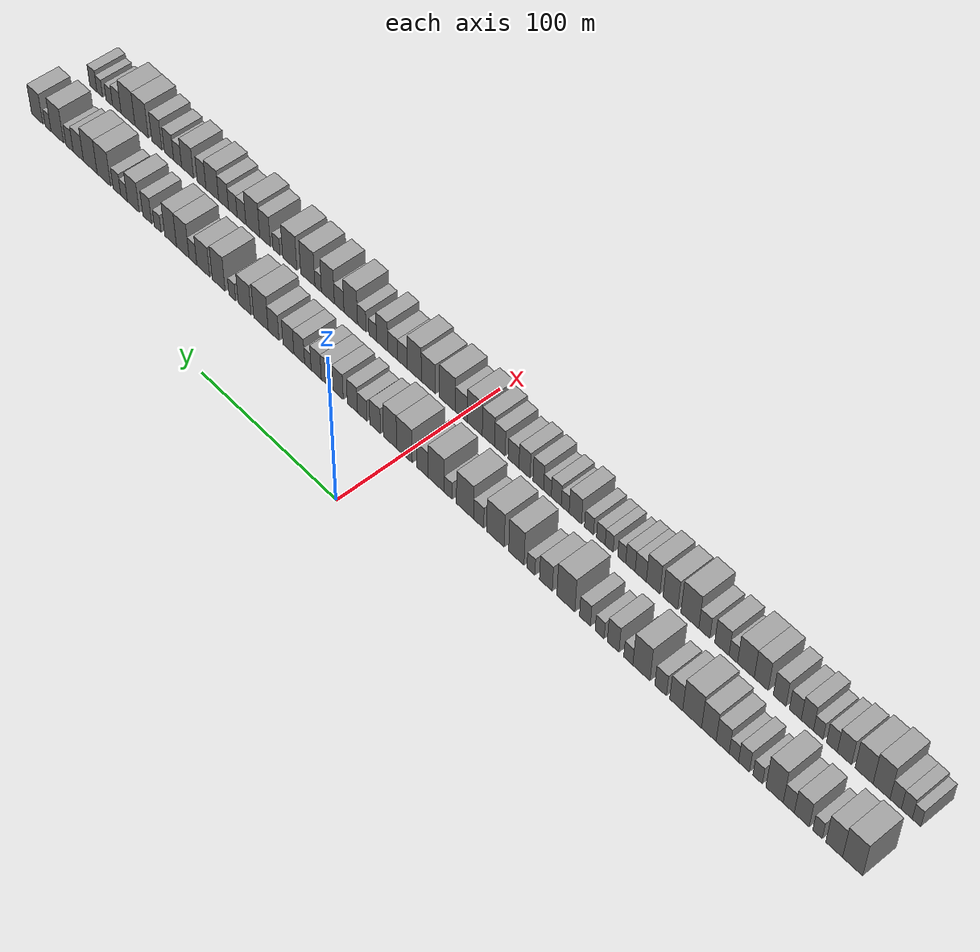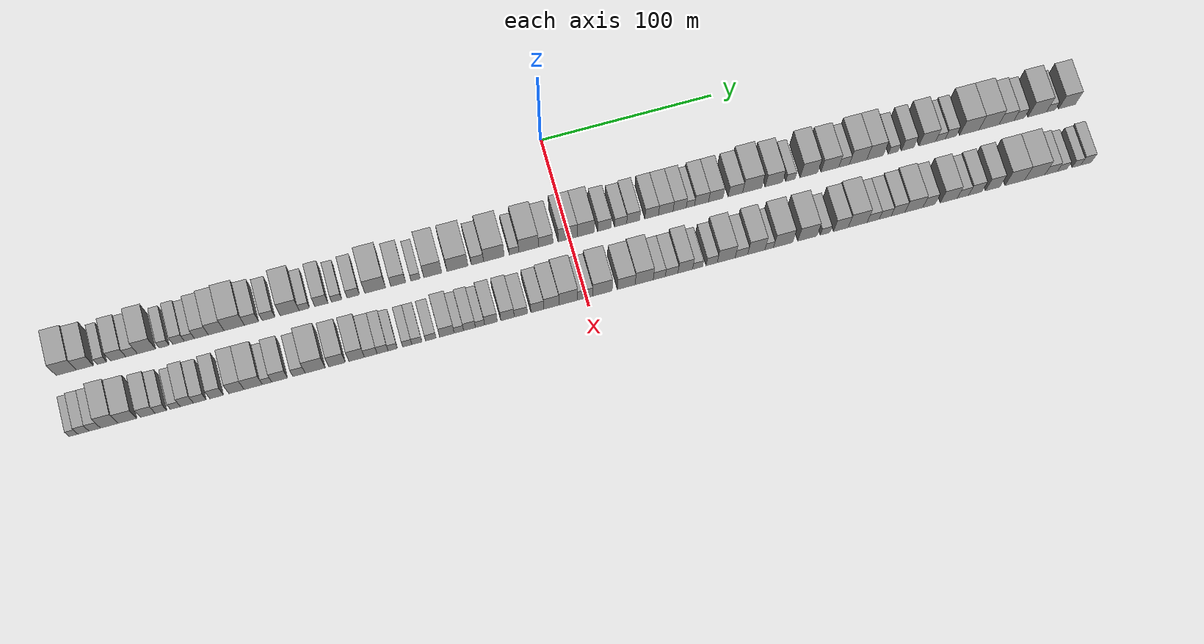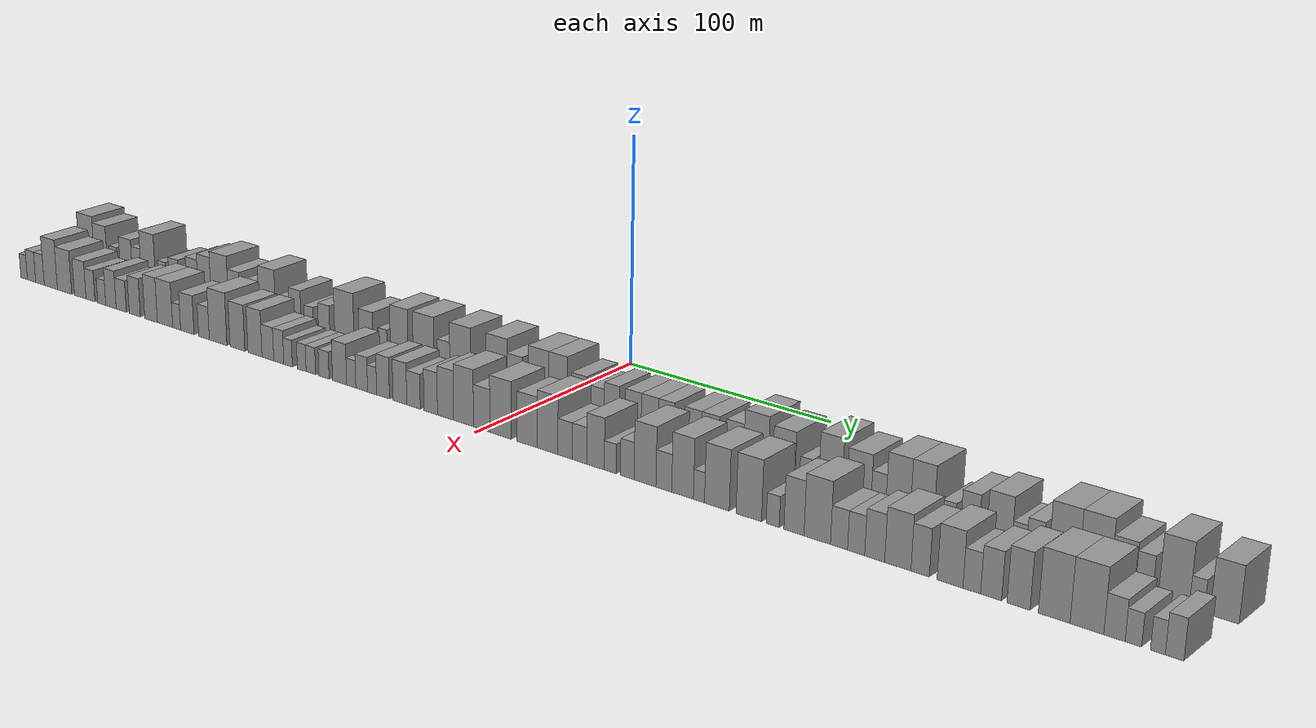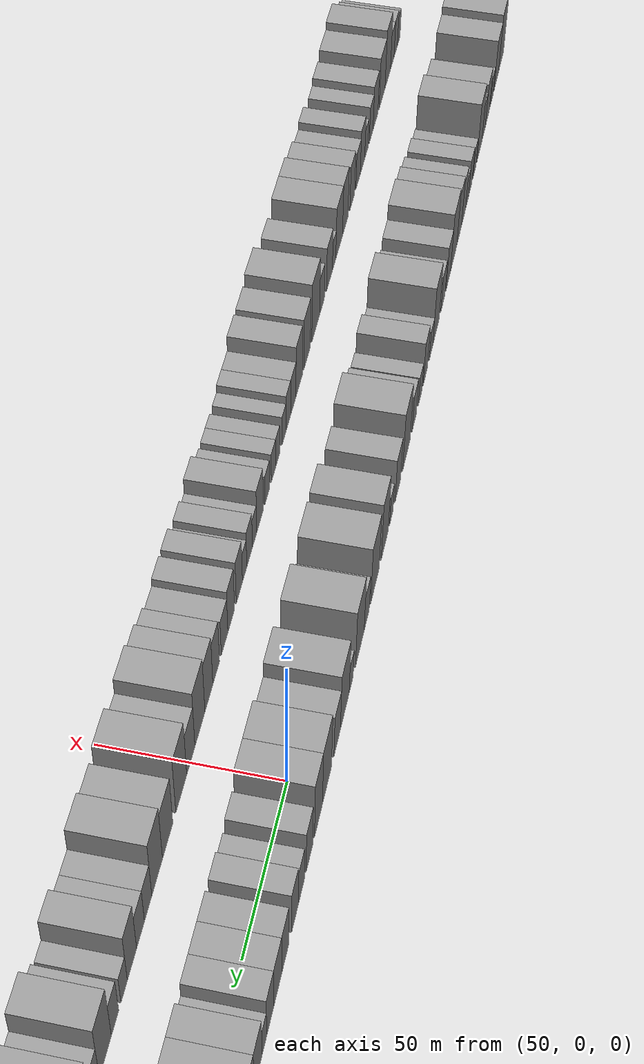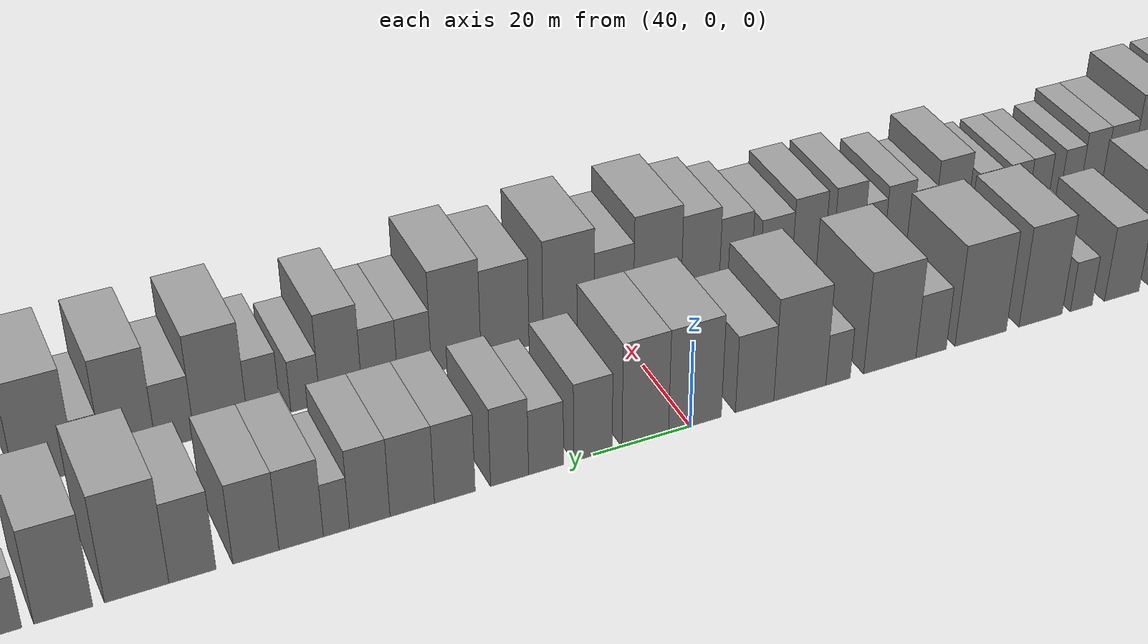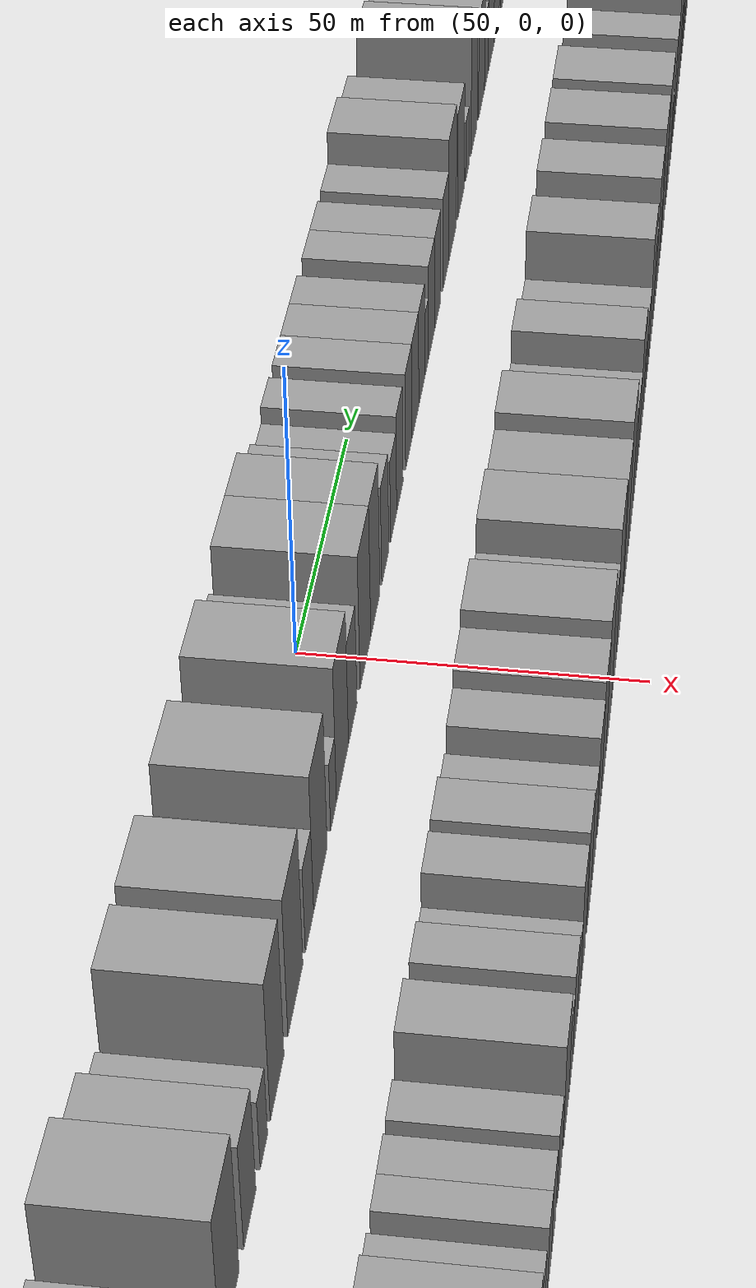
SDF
<sdf version="1.6">
 <world name="default">
  <scene>
   <sky><clouds><speed>12</speed></clouds></sky>
   <ambient>0.4 0.4 0.4 1</ambient>
   <background>0.7 0.7 0.7 1</background>
   <shadows>1</shadows>
  </scene>
  <gravity>0 0 -9.8066</gravity>
  <magnetic_field>6e-06 2.3e-05 -4.2e-05</magnetic_field>
  <physics default="0" name="default_physics" type="ode">
   <ode>
    <solver>
     <type>quick</type>
     <iters>10</iters>
     <sor>1.0</sor>
     <use_dynamic_moi_rescaling>0</use_dynamic_moi_rescaling>
    </solver>
    <constraints>
     <cfm>0</cfm>
     <erp>0.2</erp>
     <contact_max_correcting_vel>100</contact_max_correcting_vel>
     <contact_surface_layer>0.001</contact_surface_layer>
    </constraints>
   </ode>
   <max_step_size>0.004</max_step_size>
   <real_time_factor>1</real_time_factor>
   <real_time_update_rate>250</real_time_update_rate>
  </physics>
  <light name="sun" type="directional">
   <pose>0 0 10 0 0 0</pose>
   <diffuse>0.8 0.8 0.8 1</diffuse>
   <specular>0.2 0.2 0.2 1</specular>
   <attenuation>
    <range>1000</range>
    <constant>0.9</constant>
    <linear>0.01</linear>
    <quadratic>0.001</quadratic>
   </attenuation>
   <direction>-0.5 0.1 -0.9</direction>
  </light>
  <model name="building_1">
   <static>1</static>
   <pose>50.0000 -284.3537 0 0.000000 0.000000 0.000000</pose>
   <link name="link">
    <pose>0 0 12.00 0 0 0</pose>
    <collision name="collision"><geometry><box><size>20.0000 11.2926 24.0000</size></box></geometry></collision>
    <visual name="visual">
     <cast_shadows>0</cast_shadows>
     <geometry><box><size>20.0000 11.2926 24.0000</size></box></geometry>
     <material>
      <script>
       <uri>model://grey_wall/materials/scripts</uri>
       <uri>model://grey_wall/materials/textures</uri>
       <name>vrc/grey_wall</name>
      </script>
     </material>
    </visual>
   </link>
  </model>
  <model name="building_2">
   <static>1</static>
   <pose>50.0000 -273.9467 0 0.000000 0.000000 0.000000</pose>
   <link name="link">
    <pose>0 0 10.50 0 0 0</pose>
    <collision name="collision"><geometry><box><size>20.0000 9.5215 21.0000</size></box></geometry></collision>
    <visual name="visual">
     <cast_shadows>0</cast_shadows>
     <geometry><box><size>20.0000 9.5215 21.0000</size></box></geometry>
     <material>
      <script>
       <uri>model://grey_wall/materials/scripts</uri>
       <uri>model://grey_wall/materials/textures</uri>
       <name>vrc/grey_wall</name>
      </script>
     </material>
    </visual>
   </link>
  </model>
  <model name="building_3">
   <static>1</static>
   <pose>50.0000 -264.4770 0 0.000000 0.000000 0.000000</pose>
   <link name="link">
    <pose>0 0 6.00 0 0 0</pose>
    <collision name="collision"><geometry><box><size>20.0000 5.4179 12.0000</size></box></geometry></collision>
    <visual name="visual">
     <cast_shadows>0</cast_shadows>
     <geometry><box><size>20.0000 5.4179 12.0000</size></box></geometry>
     <material>
      <script>
       <uri>model://grey_wall/materials/scripts</uri>
       <uri>model://grey_wall/materials/textures</uri>
       <name>vrc/grey_wall</name>
      </script>
     </material>
    </visual>
   </link>
  </model>
  <model name="building_4">
   <static>1</static>
   <pose>50.0000 -255.4573 0 0.000000 0.000000 0.000000</pose>
   <link name="link">
    <pose>0 0 9.00 0 0 0</pose>
    <collision name="collision"><geometry><box><size>20.0000 8.6215 18.0000</size></box></geometry></collision>
    <visual name="visual">
     <cast_shadows>0</cast_shadows>
     <geometry><box><size>20.0000 8.6215 18.0000</size></box></geometry>
     <material>
      <script>
       <uri>model://grey_wall/materials/scripts</uri>
       <uri>model://grey_wall/materials/textures</uri>
       <name>vrc/grey_wall</name>
      </script>
     </material>
    </visual>
   </link>
  </model>
  <model name="building_5">
   <static>1</static>
   <pose>50.0000 -247.9118 0 0.000000 0.000000 0.000000</pose>
   <link name="link">
    <pose>0 0 7.50 0 0 0</pose>
    <collision name="collision"><geometry><box><size>20.0000 6.4694 15.0000</size></box></geometry></collision>
    <visual name="visual">
     <cast_shadows>0</cast_shadows>
     <geometry><box><size>20.0000 6.4694 15.0000</size></box></geometry>
     <material>
      <script>
       <uri>model://grey_wall/materials/scripts</uri>
       <uri>model://grey_wall/materials/textures</uri>
       <name>vrc/grey_wall</name>
      </script>
     </material>
    </visual>
   </link>
  </model>
  <model name="building_6">
   <static>1</static>
   <pose>50.0000 -239.6142 0 0.000000 0.000000 0.000000</pose>
   <link name="link">
    <pose>0 0 12.00 0 0 0</pose>
    <collision name="collision"><geometry><box><size>20.0000 10.1259 24.0000</size></box></geometry></collision>
    <visual name="visual">
     <cast_shadows>0</cast_shadows>
     <geometry><box><size>20.0000 10.1259 24.0000</size></box></geometry>
     <material>
      <script>
       <uri>model://grey_wall/materials/scripts</uri>
       <uri>model://grey_wall/materials/textures</uri>
       <name>vrc/grey_wall</name>
      </script>
     </material>
    </visual>
   </link>
  </model>
  <model name="building_7">
   <static>1</static>
   <pose>50.0000 -229.7362 0 0.000000 0.000000 0.000000</pose>
   <link name="link">
    <pose>0 0 6.00 0 0 0</pose>
    <collision name="collision"><geometry><box><size>20.0000 5.6300 12.0000</size></box></geometry></collision>
    <visual name="visual">
     <cast_shadows>0</cast_shadows>
     <geometry><box><size>20.0000 5.6300 12.0000</size></box></geometry>
     <material>
      <script>
       <uri>model://grey_wall/materials/scripts</uri>
       <uri>model://grey_wall/materials/textures</uri>
       <name>vrc/grey_wall</name>
      </script>
     </material>
    </visual>
   </link>
  </model>
  <model name="building_8">
   <static>1</static>
   <pose>50.0000 -221.6639 0 0.000000 0.000000 0.000000</pose>
   <link name="link">
    <pose>0 0 7.50 0 0 0</pose>
    <collision name="collision"><geometry><box><size>20.0000 6.5146 15.0000</size></box></geometry></collision>
    <visual name="visual">
     <cast_shadows>0</cast_shadows>
     <geometry><box><size>20.0000 6.5146 15.0000</size></box></geometry>
     <material>
      <script>
       <uri>model://grey_wall/materials/scripts</uri>
       <uri>model://grey_wall/materials/textures</uri>
       <name>vrc/grey_wall</name>
      </script>
     </material>
    </visual>
   </link>
  </model>
  <model name="building_9">
   <static>1</static>
   <pose>50.0000 -215.6207 0 0.000000 0.000000 0.000000</pose>
   <link name="link">
    <pose>0 0 6.00 0 0 0</pose>
    <collision name="collision"><geometry><box><size>20.0000 5.5718 12.0000</size></box></geometry></collision>
    <visual name="visual">
     <cast_shadows>0</cast_shadows>
     <geometry><box><size>20.0000 5.5718 12.0000</size></box></geometry>
     <material>
      <script>
       <uri>model://grey_wall/materials/scripts</uri>
       <uri>model://grey_wall/materials/textures</uri>
       <name>vrc/grey_wall</name>
      </script>
     </material>
    </visual>
   </link>
  </model>
  <model name="building_10">
   <static>1</static>
   <pose>50.0000 -208.9223 0 0.000000 0.000000 0.000000</pose>
   <link name="link">
    <pose>0 0 9.00 0 0 0</pose>
    <collision name="collision"><geometry><box><size>20.0000 7.8251 18.0000</size></box></geometry></collision>
    <visual name="visual">
     <cast_shadows>0</cast_shadows>
     <geometry><box><size>20.0000 7.8251 18.0000</size></box></geometry>
     <material>
      <script>
       <uri>model://grey_wall/materials/scripts</uri>
       <uri>model://grey_wall/materials/textures</uri>
       <name>vrc/grey_wall</name>
      </script>
     </material>
    </visual>
   </link>
  </model>
  <model name="building_11">
   <static>1</static>
   <pose>50.0000 -200.6276 0 0.000000 0.000000 0.000000</pose>
   <link name="link">
    <pose>0 0 10.50 0 0 0</pose>
    <collision name="collision"><geometry><box><size>20.0000 8.7643 21.0000</size></box></geometry></collision>
    <visual name="visual">
     <cast_shadows>0</cast_shadows>
     <geometry><box><size>20.0000 8.7643 21.0000</size></box></geometry>
     <material>
      <script>
       <uri>model://grey_wall/materials/scripts</uri>
       <uri>model://grey_wall/materials/textures</uri>
       <name>vrc/grey_wall</name>
      </script>
     </material>
    </visual>
   </link>
  </model>
  <model name="building_12">
   <static>1</static>
   <pose>50.0000 -190.4889 0 0.000000 0.000000 0.000000</pose>
   <link name="link">
    <pose>0 0 12.00 0 0 0</pose>
    <collision name="collision"><geometry><box><size>20.0000 11.5131 24.0000</size></box></geometry></collision>
    <visual name="visual">
     <cast_shadows>0</cast_shadows>
     <geometry><box><size>20.0000 11.5131 24.0000</size></box></geometry>
     <material>
      <script>
       <uri>model://grey_wall/materials/scripts</uri>
       <uri>model://grey_wall/materials/textures</uri>
       <name>vrc/grey_wall</name>
      </script>
     </material>
    </visual>
   </link>
  </model>
  <model name="building_13">
   <static>1</static>
   <pose>50.0000 -180.7489 0 0.000000 0.000000 0.000000</pose>
   <link name="link">
    <pose>0 0 9.00 0 0 0</pose>
    <collision name="collision"><geometry><box><size>20.0000 7.9670 18.0000</size></box></geometry></collision>
    <visual name="visual">
     <cast_shadows>0</cast_shadows>
     <geometry><box><size>20.0000 7.9670 18.0000</size></box></geometry>
     <material>
      <script>
       <uri>model://grey_wall/materials/scripts</uri>
       <uri>model://grey_wall/materials/textures</uri>
       <name>vrc/grey_wall</name>
      </script>
     </material>
    </visual>
   </link>
  </model>
  <model name="building_14">
   <static>1</static>
   <pose>50.0000 -171.1622 0 0.000000 0.000000 0.000000</pose>
   <link name="link">
    <pose>0 0 7.50 0 0 0</pose>
    <collision name="collision"><geometry><box><size>20.0000 7.2064 15.0000</size></box></geometry></collision>
    <visual name="visual">
     <cast_shadows>0</cast_shadows>
     <geometry><box><size>20.0000 7.2064 15.0000</size></box></geometry>
     <material>
      <script>
       <uri>model://grey_wall/materials/scripts</uri>
       <uri>model://grey_wall/materials/textures</uri>
       <name>vrc/grey_wall</name>
      </script>
     </material>
    </visual>
   </link>
  </model>
  <model name="building_15">
   <static>1</static>
   <pose>50.0000 -159.1854 0 0.000000 0.000000 0.000000</pose>
   <link name="link">
    <pose>0 0 12.00 0 0 0</pose>
    <collision name="collision"><geometry><box><size>20.0000 10.7472 24.0000</size></box></geometry></collision>
    <visual name="visual">
     <cast_shadows>0</cast_shadows>
     <geometry><box><size>20.0000 10.7472 24.0000</size></box></geometry>
     <material>
      <script>
       <uri>model://grey_wall/materials/scripts</uri>
       <uri>model://grey_wall/materials/textures</uri>
       <name>vrc/grey_wall</name>
      </script>
     </material>
    </visual>
   </link>
  </model>
  <model name="building_16">
   <static>1</static>
   <pose>50.0000 -150.9458 0 0.000000 0.000000 0.000000</pose>
   <link name="link">
    <pose>0 0 6.00 0 0 0</pose>
    <collision name="collision"><geometry><box><size>20.0000 5.7321 12.0000</size></box></geometry></collision>
    <visual name="visual">
     <cast_shadows>0</cast_shadows>
     <geometry><box><size>20.0000 5.7321 12.0000</size></box></geometry>
     <material>
      <script>
       <uri>model://grey_wall/materials/scripts</uri>
       <uri>model://grey_wall/materials/textures</uri>
       <name>vrc/grey_wall</name>
      </script>
     </material>
    </visual>
   </link>
  </model>
  <model name="building_17">
   <static>1</static>
   <pose>50.0000 -141.3510 0 0.000000 0.000000 0.000000</pose>
   <link name="link">
    <pose>0 0 9.00 0 0 0</pose>
    <collision name="collision"><geometry><box><size>20.0000 7.4574 18.0000</size></box></geometry></collision>
    <visual name="visual">
     <cast_shadows>0</cast_shadows>
     <geometry><box><size>20.0000 7.4574 18.0000</size></box></geometry>
     <material>
      <script>
       <uri>model://grey_wall/materials/scripts</uri>
       <uri>model://grey_wall/materials/textures</uri>
       <name>vrc/grey_wall</name>
      </script>
     </material>
    </visual>
   </link>
  </model>
  <model name="building_18">
   <static>1</static>
   <pose>50.0000 -132.7311 0 0.000000 0.000000 0.000000</pose>
   <link name="link">
    <pose>0 0 6.00 0 0 0</pose>
    <collision name="collision"><geometry><box><size>20.0000 5.7824 12.0000</size></box></geometry></collision>
    <visual name="visual">
     <cast_shadows>0</cast_shadows>
     <geometry><box><size>20.0000 5.7824 12.0000</size></box></geometry>
     <material>
      <script>
       <uri>model://grey_wall/materials/scripts</uri>
       <uri>model://grey_wall/materials/textures</uri>
       <name>vrc/grey_wall</name>
      </script>
     </material>
    </visual>
   </link>
  </model>
  <model name="building_19">
   <static>1</static>
   <pose>50.0000 -123.3128 0 0.000000 0.000000 0.000000</pose>
   <link name="link">
    <pose>0 0 7.50 0 0 0</pose>
    <collision name="collision"><geometry><box><size>20.0000 7.0542 15.0000</size></box></geometry></collision>
    <visual name="visual">
     <cast_shadows>0</cast_shadows>
     <geometry><box><size>20.0000 7.0542 15.0000</size></box></geometry>
     <material>
      <script>
       <uri>model://grey_wall/materials/scripts</uri>
       <uri>model://grey_wall/materials/textures</uri>
       <name>vrc/grey_wall</name>
      </script>
     </material>
    </visual>
   </link>
  </model>
  <model name="building_20">
   <static>1</static>
   <pose>50.0000 -110.9050 0 0.000000 0.000000 0.000000</pose>
   <link name="link">
    <pose>0 0 12.00 0 0 0</pose>
    <collision name="collision"><geometry><box><size>20.0000 11.7614 24.0000</size></box></geometry></collision>
    <visual name="visual">
     <cast_shadows>0</cast_shadows>
     <geometry><box><size>20.0000 11.7614 24.0000</size></box></geometry>
     <material>
      <script>
       <uri>model://grey_wall/materials/scripts</uri>
       <uri>model://grey_wall/materials/textures</uri>
       <name>vrc/grey_wall</name>
      </script>
     </material>
    </visual>
   </link>
  </model>
  <model name="building_21">
   <static>1</static>
   <pose>50.0000 -97.8067 0 0.000000 0.000000 0.000000</pose>
   <link name="link">
    <pose>0 0 9.00 0 0 0</pose>
    <collision name="collision"><geometry><box><size>20.0000 8.4354 18.0000</size></box></geometry></collision>
    <visual name="visual">
     <cast_shadows>0</cast_shadows>
     <geometry><box><size>20.0000 8.4354 18.0000</size></box></geometry>
     <material>
      <script>
       <uri>model://grey_wall/materials/scripts</uri>
       <uri>model://grey_wall/materials/textures</uri>
       <name>vrc/grey_wall</name>
      </script>
     </material>
    </visual>
   </link>
  </model>
  <model name="building_22">
   <static>1</static>
   <pose>50.0000 -87.9572 0 0.000000 0.000000 0.000000</pose>
   <link name="link">
    <pose>0 0 6.00 0 0 0</pose>
    <collision name="collision"><geometry><box><size>20.0000 5.2635 12.0000</size></box></geometry></collision>
    <visual name="visual">
     <cast_shadows>0</cast_shadows>
     <geometry><box><size>20.0000 5.2635 12.0000</size></box></geometry>
     <material>
      <script>
       <uri>model://grey_wall/materials/scripts</uri>
       <uri>model://grey_wall/materials/textures</uri>
       <name>vrc/grey_wall</name>
      </script>
     </material>
    </visual>
   </link>
  </model>
  <model name="building_23">
   <static>1</static>
   <pose>50.0000 -78.1997 0 0.000000 0.000000 0.000000</pose>
   <link name="link">
    <pose>0 0 12.00 0 0 0</pose>
    <collision name="collision"><geometry><box><size>20.0000 10.2516 24.0000</size></box></geometry></collision>
    <visual name="visual">
     <cast_shadows>0</cast_shadows>
     <geometry><box><size>20.0000 10.2516 24.0000</size></box></geometry>
     <material>
      <script>
       <uri>model://grey_wall/materials/scripts</uri>
       <uri>model://grey_wall/materials/textures</uri>
       <name>vrc/grey_wall</name>
      </script>
     </material>
    </visual>
   </link>
  </model>
  <model name="building_24">
   <static>1</static>
   <pose>50.0000 -64.1104 0 0.000000 0.000000 0.000000</pose>
   <link name="link">
    <pose>0 0 12.00 0 0 0</pose>
    <collision name="collision"><geometry><box><size>20.0000 11.9269 24.0000</size></box></geometry></collision>
    <visual name="visual">
     <cast_shadows>0</cast_shadows>
     <geometry><box><size>20.0000 11.9269 24.0000</size></box></geometry>
     <material>
      <script>
       <uri>model://grey_wall/materials/scripts</uri>
       <uri>model://grey_wall/materials/textures</uri>
       <name>vrc/grey_wall</name>
      </script>
     </material>
    </visual>
   </link>
  </model>
  <model name="building_25">
   <static>1</static>
   <pose>50.0000 -52.6682 0 0.000000 0.000000 0.000000</pose>
   <link name="link">
    <pose>0 0 7.50 0 0 0</pose>
    <collision name="collision"><geometry><box><size>20.0000 6.9575 15.0000</size></box></geometry></collision>
    <visual name="visual">
     <cast_shadows>0</cast_shadows>
     <geometry><box><size>20.0000 6.9575 15.0000</size></box></geometry>
     <material>
      <script>
       <uri>model://grey_wall/materials/scripts</uri>
       <uri>model://grey_wall/materials/textures</uri>
       <name>vrc/grey_wall</name>
      </script>
     </material>
    </visual>
   </link>
  </model>
  <model name="building_26">
   <static>1</static>
   <pose>50.0000 -43.3174 0 0.000000 0.000000 0.000000</pose>
   <link name="link">
    <pose>0 0 12.00 0 0 0</pose>
    <collision name="collision"><geometry><box><size>20.0000 11.7442 24.0000</size></box></geometry></collision>
    <visual name="visual">
     <cast_shadows>0</cast_shadows>
     <geometry><box><size>20.0000 11.7442 24.0000</size></box></geometry>
     <material>
      <script>
       <uri>model://grey_wall/materials/scripts</uri>
       <uri>model://grey_wall/materials/textures</uri>
       <name>vrc/grey_wall</name>
      </script>
     </material>
    </visual>
   </link>
  </model>
  <model name="building_27">
   <static>1</static>
   <pose>50.0000 -31.7545 0 0.000000 0.000000 0.000000</pose>
   <link name="link">
    <pose>0 0 6.00 0 0 0</pose>
    <collision name="collision"><geometry><box><size>20.0000 5.3816 12.0000</size></box></geometry></collision>
    <visual name="visual">
     <cast_shadows>0</cast_shadows>
     <geometry><box><size>20.0000 5.3816 12.0000</size></box></geometry>
     <material>
      <script>
       <uri>model://grey_wall/materials/scripts</uri>
       <uri>model://grey_wall/materials/textures</uri>
       <name>vrc/grey_wall</name>
      </script>
     </material>
    </visual>
   </link>
  </model>
  <model name="building_28">
   <static>1</static>
   <pose>50.0000 -23.3864 0 0.000000 0.000000 0.000000</pose>
   <link name="link">
    <pose>0 0 12.00 0 0 0</pose>
    <collision name="collision"><geometry><box><size>20.0000 11.3546 24.0000</size></box></geometry></collision>
    <visual name="visual">
     <cast_shadows>0</cast_shadows>
     <geometry><box><size>20.0000 11.3546 24.0000</size></box></geometry>
     <material>
      <script>
       <uri>model://grey_wall/materials/scripts</uri>
       <uri>model://grey_wall/materials/textures</uri>
       <name>vrc/grey_wall</name>
      </script>
     </material>
    </visual>
   </link>
  </model>
  <model name="building_29">
   <static>1</static>
   <pose>50.0000 -13.5969 0 0.000000 0.000000 0.000000</pose>
   <link name="link">
    <pose>0 0 9.00 0 0 0</pose>
    <collision name="collision"><geometry><box><size>20.0000 8.2244 18.0000</size></box></geometry></collision>
    <visual name="visual">
     <cast_shadows>0</cast_shadows>
     <geometry><box><size>20.0000 8.2244 18.0000</size></box></geometry>
     <material>
      <script>
       <uri>model://grey_wall/materials/scripts</uri>
       <uri>model://grey_wall/materials/textures</uri>
       <name>vrc/grey_wall</name>
      </script>
     </material>
    </visual>
   </link>
  </model>
  <model name="building_30">
   <static>1</static>
   <pose>50.0000 -0.9442 0 0.000000 0.000000 0.000000</pose>
   <link name="link">
    <pose>0 0 12.00 0 0 0</pose>
    <collision name="collision"><geometry><box><size>20.0000 11.0809 24.0000</size></box></geometry></collision>
    <visual name="visual">
     <cast_shadows>0</cast_shadows>
     <geometry><box><size>20.0000 11.0809 24.0000</size></box></geometry>
     <material>
      <script>
       <uri>model://grey_wall/materials/scripts</uri>
       <uri>model://grey_wall/materials/textures</uri>
       <name>vrc/grey_wall</name>
      </script>
     </material>
    </visual>
   </link>
  </model>
  <model name="building_31">
   <static>1</static>
   <pose>50.0000 9.4016 0 0.000000 0.000000 0.000000</pose>
   <link name="link">
    <pose>0 0 12.00 0 0 0</pose>
    <collision name="collision"><geometry><box><size>20.0000 9.6106 24.0000</size></box></geometry></collision>
    <visual name="visual">
     <cast_shadows>0</cast_shadows>
     <geometry><box><size>20.0000 9.6106 24.0000</size></box></geometry>
     <material>
      <script>
       <uri>model://grey_wall/materials/scripts</uri>
       <uri>model://grey_wall/materials/textures</uri>
       <name>vrc/grey_wall</name>
      </script>
     </material>
    </visual>
   </link>
  </model>
  <model name="building_32">
   <static>1</static>
   <pose>50.0000 20.1189 0 0.000000 0.000000 0.000000</pose>
   <link name="link">
    <pose>0 0 9.00 0 0 0</pose>
    <collision name="collision"><geometry><box><size>20.0000 7.8241 18.0000</size></box></geometry></collision>
    <visual name="visual">
     <cast_shadows>0</cast_shadows>
     <geometry><box><size>20.0000 7.8241 18.0000</size></box></geometry>
     <material>
      <script>
       <uri>model://grey_wall/materials/scripts</uri>
       <uri>model://grey_wall/materials/textures</uri>
       <name>vrc/grey_wall</name>
      </script>
     </material>
    </visual>
   </link>
  </model>
  <model name="building_33">
   <static>1</static>
   <pose>50.0000 29.5173 0 0.000000 0.000000 0.000000</pose>
   <link name="link">
    <pose>0 0 7.50 0 0 0</pose>
    <collision name="collision"><geometry><box><size>20.0000 6.9727 15.0000</size></box></geometry></collision>
    <visual name="visual">
     <cast_shadows>0</cast_shadows>
     <geometry><box><size>20.0000 6.9727 15.0000</size></box></geometry>
     <material>
      <script>
       <uri>model://grey_wall/materials/scripts</uri>
       <uri>model://grey_wall/materials/textures</uri>
       <name>vrc/grey_wall</name>
      </script>
     </material>
    </visual>
   </link>
  </model>
  <model name="building_34">
   <static>1</static>
   <pose>50.0000 36.7417 0 0.000000 0.000000 0.000000</pose>
   <link name="link">
    <pose>0 0 9.00 0 0 0</pose>
    <collision name="collision"><geometry><box><size>20.0000 7.4761 18.0000</size></box></geometry></collision>
    <visual name="visual">
     <cast_shadows>0</cast_shadows>
     <geometry><box><size>20.0000 7.4761 18.0000</size></box></geometry>
     <material>
      <script>
       <uri>model://grey_wall/materials/scripts</uri>
       <uri>model://grey_wall/materials/textures</uri>
       <name>vrc/grey_wall</name>
      </script>
     </material>
    </visual>
   </link>
  </model>
  <model name="building_35">
   <static>1</static>
   <pose>50.0000 47.4187 0 0.000000 0.000000 0.000000</pose>
   <link name="link">
    <pose>0 0 9.00 0 0 0</pose>
    <collision name="collision"><geometry><box><size>20.0000 7.8779 18.0000</size></box></geometry></collision>
    <visual name="visual">
     <cast_shadows>0</cast_shadows>
     <geometry><box><size>20.0000 7.8779 18.0000</size></box></geometry>
     <material>
      <script>
       <uri>model://grey_wall/materials/scripts</uri>
       <uri>model://grey_wall/materials/textures</uri>
       <name>vrc/grey_wall</name>
      </script>
     </material>
    </visual>
   </link>
  </model>
  <model name="building_36">
   <static>1</static>
   <pose>50.0000 55.5875 0 0.000000 0.000000 0.000000</pose>
   <link name="link">
    <pose>0 0 9.00 0 0 0</pose>
    <collision name="collision"><geometry><box><size>20.0000 8.4597 18.0000</size></box></geometry></collision>
    <visual name="visual">
     <cast_shadows>0</cast_shadows>
     <geometry><box><size>20.0000 8.4597 18.0000</size></box></geometry>
     <material>
      <script>
       <uri>model://grey_wall/materials/scripts</uri>
       <uri>model://grey_wall/materials/textures</uri>
       <name>vrc/grey_wall</name>
      </script>
     </material>
    </visual>
   </link>
  </model>
  <model name="building_37">
   <static>1</static>
   <pose>50.0000 63.6244 0 0.000000 0.000000 0.000000</pose>
   <link name="link">
    <pose>0 0 9.00 0 0 0</pose>
    <collision name="collision"><geometry><box><size>20.0000 7.6142 18.0000</size></box></geometry></collision>
    <visual name="visual">
     <cast_shadows>0</cast_shadows>
     <geometry><box><size>20.0000 7.6142 18.0000</size></box></geometry>
     <material>
      <script>
       <uri>model://grey_wall/materials/scripts</uri>
       <uri>model://grey_wall/materials/textures</uri>
       <name>vrc/grey_wall</name>
      </script>
     </material>
    </visual>
   </link>
  </model>
  <model name="building_38">
   <static>1</static>
   <pose>50.0000 69.8518 0 0.000000 0.000000 0.000000</pose>
   <link name="link">
    <pose>0 0 6.00 0 0 0</pose>
    <collision name="collision"><geometry><box><size>20.0000 4.8407 12.0000</size></box></geometry></collision>
    <visual name="visual">
     <cast_shadows>0</cast_shadows>
     <geometry><box><size>20.0000 4.8407 12.0000</size></box></geometry>
     <material>
      <script>
       <uri>model://grey_wall/materials/scripts</uri>
       <uri>model://grey_wall/materials/textures</uri>
       <name>vrc/grey_wall</name>
      </script>
     </material>
    </visual>
   </link>
  </model>
  <model name="building_39">
   <static>1</static>
   <pose>50.0000 76.3494 0 0.000000 0.000000 0.000000</pose>
   <link name="link">
    <pose>0 0 9.00 0 0 0</pose>
    <collision name="collision"><geometry><box><size>20.0000 8.1544 18.0000</size></box></geometry></collision>
    <visual name="visual">
     <cast_shadows>0</cast_shadows>
     <geometry><box><size>20.0000 8.1544 18.0000</size></box></geometry>
     <material>
      <script>
       <uri>model://grey_wall/materials/scripts</uri>
       <uri>model://grey_wall/materials/textures</uri>
       <name>vrc/grey_wall</name>
      </script>
     </material>
    </visual>
   </link>
  </model>
  <model name="building_40">
   <static>1</static>
   <pose>50.0000 84.6079 0 0.000000 0.000000 0.000000</pose>
   <link name="link">
    <pose>0 0 9.00 0 0 0</pose>
    <collision name="collision"><geometry><box><size>20.0000 8.3627 18.0000</size></box></geometry></collision>
    <visual name="visual">
     <cast_shadows>0</cast_shadows>
     <geometry><box><size>20.0000 8.3627 18.0000</size></box></geometry>
     <material>
      <script>
       <uri>model://grey_wall/materials/scripts</uri>
       <uri>model://grey_wall/materials/textures</uri>
       <name>vrc/grey_wall</name>
      </script>
     </material>
    </visual>
   </link>
  </model>
  <model name="building_41">
   <static>1</static>
   <pose>50.0000 95.9623 0 0.000000 0.000000 0.000000</pose>
   <link name="link">
    <pose>0 0 9.00 0 0 0</pose>
    <collision name="collision"><geometry><box><size>20.0000 8.3461 18.0000</size></box></geometry></collision>
    <visual name="visual">
     <cast_shadows>0</cast_shadows>
     <geometry><box><size>20.0000 8.3461 18.0000</size></box></geometry>
     <material>
      <script>
       <uri>model://grey_wall/materials/scripts</uri>
       <uri>model://grey_wall/materials/textures</uri>
       <name>vrc/grey_wall</name>
      </script>
     </material>
    </visual>
   </link>
  </model>
  <model name="building_42">
   <static>1</static>
   <pose>50.0000 105.7547 0 0.000000 0.000000 0.000000</pose>
   <link name="link">
    <pose>0 0 12.00 0 0 0</pose>
    <collision name="collision"><geometry><box><size>20.0000 11.2388 24.0000</size></box></geometry></collision>
    <visual name="visual">
     <cast_shadows>0</cast_shadows>
     <geometry><box><size>20.0000 11.2388 24.0000</size></box></geometry>
     <material>
      <script>
       <uri>model://grey_wall/materials/scripts</uri>
       <uri>model://grey_wall/materials/textures</uri>
       <name>vrc/grey_wall</name>
      </script>
     </material>
    </visual>
   </link>
  </model>
  <model name="building_43">
   <static>1</static>
   <pose>50.0000 118.3998 0 0.000000 0.000000 0.000000</pose>
   <link name="link">
    <pose>0 0 10.50 0 0 0</pose>
    <collision name="collision"><geometry><box><size>20.0000 10.0513 21.0000</size></box></geometry></collision>
    <visual name="visual">
     <cast_shadows>0</cast_shadows>
     <geometry><box><size>20.0000 10.0513 21.0000</size></box></geometry>
     <material>
      <script>
       <uri>model://grey_wall/materials/scripts</uri>
       <uri>model://grey_wall/materials/textures</uri>
       <name>vrc/grey_wall</name>
      </script>
     </material>
    </visual>
   </link>
  </model>
  <model name="building_44">
   <static>1</static>
   <pose>50.0000 128.1197 0 0.000000 0.000000 0.000000</pose>
   <link name="link">
    <pose>0 0 6.00 0 0 0</pose>
    <collision name="collision"><geometry><box><size>20.0000 5.3886 12.0000</size></box></geometry></collision>
    <visual name="visual">
     <cast_shadows>0</cast_shadows>
     <geometry><box><size>20.0000 5.3886 12.0000</size></box></geometry>
     <material>
      <script>
       <uri>model://grey_wall/materials/scripts</uri>
       <uri>model://grey_wall/materials/textures</uri>
       <name>vrc/grey_wall</name>
      </script>
     </material>
    </visual>
   </link>
  </model>
  <model name="building_45">
   <static>1</static>
   <pose>50.0000 138.9003 0 0.000000 0.000000 0.000000</pose>
   <link name="link">
    <pose>0 0 12.00 0 0 0</pose>
    <collision name="collision"><geometry><box><size>20.0000 10.1726 24.0000</size></box></geometry></collision>
    <visual name="visual">
     <cast_shadows>0</cast_shadows>
     <geometry><box><size>20.0000 10.1726 24.0000</size></box></geometry>
     <material>
      <script>
       <uri>model://grey_wall/materials/scripts</uri>
       <uri>model://grey_wall/materials/textures</uri>
       <name>vrc/grey_wall</name>
      </script>
     </material>
    </visual>
   </link>
  </model>
  <model name="building_46">
   <static>1</static>
   <pose>50.0000 151.1847 0 0.000000 0.000000 0.000000</pose>
   <link name="link">
    <pose>0 0 10.50 0 0 0</pose>
    <collision name="collision"><geometry><box><size>20.0000 10.3962 21.0000</size></box></geometry></collision>
    <visual name="visual">
     <cast_shadows>0</cast_shadows>
     <geometry><box><size>20.0000 10.3962 21.0000</size></box></geometry>
     <material>
      <script>
       <uri>model://grey_wall/materials/scripts</uri>
       <uri>model://grey_wall/materials/textures</uri>
       <name>vrc/grey_wall</name>
      </script>
     </material>
    </visual>
   </link>
  </model>
  <model name="building_47">
   <static>1</static>
   <pose>50.0000 159.4917 0 0.000000 0.000000 0.000000</pose>
   <link name="link">
    <pose>0 0 7.50 0 0 0</pose>
    <collision name="collision"><geometry><box><size>20.0000 6.2178 15.0000</size></box></geometry></collision>
    <visual name="visual">
     <cast_shadows>0</cast_shadows>
     <geometry><box><size>20.0000 6.2178 15.0000</size></box></geometry>
     <material>
      <script>
       <uri>model://grey_wall/materials/scripts</uri>
       <uri>model://grey_wall/materials/textures</uri>
       <name>vrc/grey_wall</name>
      </script>
     </material>
    </visual>
   </link>
  </model>
  <model name="building_48">
   <static>1</static>
   <pose>50.0000 167.7055 0 0.000000 0.000000 0.000000</pose>
   <link name="link">
    <pose>0 0 12.00 0 0 0</pose>
    <collision name="collision"><geometry><box><size>20.0000 10.2099 24.0000</size></box></geometry></collision>
    <visual name="visual">
     <cast_shadows>0</cast_shadows>
     <geometry><box><size>20.0000 10.2099 24.0000</size></box></geometry>
     <material>
      <script>
       <uri>model://grey_wall/materials/scripts</uri>
       <uri>model://grey_wall/materials/textures</uri>
       <name>vrc/grey_wall</name>
      </script>
     </material>
    </visual>
   </link>
  </model>
  <model name="building_49">
   <static>1</static>
   <pose>50.0000 177.6458 0 0.000000 0.000000 0.000000</pose>
   <link name="link">
    <pose>0 0 12.00 0 0 0</pose>
    <collision name="collision"><geometry><box><size>20.0000 9.6705 24.0000</size></box></geometry></collision>
    <visual name="visual">
     <cast_shadows>0</cast_shadows>
     <geometry><box><size>20.0000 9.6705 24.0000</size></box></geometry>
     <material>
      <script>
       <uri>model://grey_wall/materials/scripts</uri>
       <uri>model://grey_wall/materials/textures</uri>
       <name>vrc/grey_wall</name>
      </script>
     </material>
    </visual>
   </link>
  </model>
  <model name="building_50">
   <static>1</static>
   <pose>50.0000 188.3380 0 0.000000 0.000000 0.000000</pose>
   <link name="link">
    <pose>0 0 6.00 0 0 0</pose>
    <collision name="collision"><geometry><box><size>20.0000 5.7140 12.0000</size></box></geometry></collision>
    <visual name="visual">
     <cast_shadows>0</cast_shadows>
     <geometry><box><size>20.0000 5.7140 12.0000</size></box></geometry>
     <material>
      <script>
       <uri>model://grey_wall/materials/scripts</uri>
       <uri>model://grey_wall/materials/textures</uri>
       <name>vrc/grey_wall</name>
      </script>
     </material>
    </visual>
   </link>
  </model>
  <model name="building_51">
   <static>1</static>
   <pose>50.0000 196.8717 0 0.000000 0.000000 0.000000</pose>
   <link name="link">
    <pose>0 0 9.00 0 0 0</pose>
    <collision name="collision"><geometry><box><size>20.0000 7.3533 18.0000</size></box></geometry></collision>
    <visual name="visual">
     <cast_shadows>0</cast_shadows>
     <geometry><box><size>20.0000 7.3533 18.0000</size></box></geometry>
     <material>
      <script>
       <uri>model://grey_wall/materials/scripts</uri>
       <uri>model://grey_wall/materials/textures</uri>
       <name>vrc/grey_wall</name>
      </script>
     </material>
    </visual>
   </link>
  </model>
  <model name="building_52">
   <static>1</static>
   <pose>50.0000 208.5047 0 0.000000 0.000000 0.000000</pose>
   <link name="link">
    <pose>0 0 10.50 0 0 0</pose>
    <collision name="collision"><geometry><box><size>20.0000 9.9125 21.0000</size></box></geometry></collision>
    <visual name="visual">
     <cast_shadows>0</cast_shadows>
     <geometry><box><size>20.0000 9.9125 21.0000</size></box></geometry>
     <material>
      <script>
       <uri>model://grey_wall/materials/scripts</uri>
       <uri>model://grey_wall/materials/textures</uri>
       <name>vrc/grey_wall</name>
      </script>
     </material>
    </visual>
   </link>
  </model>
  <model name="building_53">
   <static>1</static>
   <pose>50.0000 216.2684 0 0.000000 0.000000 0.000000</pose>
   <link name="link">
    <pose>0 0 6.00 0 0 0</pose>
    <collision name="collision"><geometry><box><size>20.0000 5.6150 12.0000</size></box></geometry></collision>
    <visual name="visual">
     <cast_shadows>0</cast_shadows>
     <geometry><box><size>20.0000 5.6150 12.0000</size></box></geometry>
     <material>
      <script>
       <uri>model://grey_wall/materials/scripts</uri>
       <uri>model://grey_wall/materials/textures</uri>
       <name>vrc/grey_wall</name>
      </script>
     </material>
    </visual>
   </link>
  </model>
  <model name="building_54">
   <static>1</static>
   <pose>50.0000 222.3416 0 0.000000 0.000000 0.000000</pose>
   <link name="link">
    <pose>0 0 7.50 0 0 0</pose>
    <collision name="collision"><geometry><box><size>20.0000 6.5314 15.0000</size></box></geometry></collision>
    <visual name="visual">
     <cast_shadows>0</cast_shadows>
     <geometry><box><size>20.0000 6.5314 15.0000</size></box></geometry>
     <material>
      <script>
       <uri>model://grey_wall/materials/scripts</uri>
       <uri>model://grey_wall/materials/textures</uri>
       <name>vrc/grey_wall</name>
      </script>
     </material>
    </visual>
   </link>
  </model>
  <model name="building_55">
   <static>1</static>
   <pose>50.0000 233.3606 0 0.000000 0.000000 0.000000</pose>
   <link name="link">
    <pose>0 0 12.00 0 0 0</pose>
    <collision name="collision"><geometry><box><size>20.0000 11.5067 24.0000</size></box></geometry></collision>
    <visual name="visual">
     <cast_shadows>0</cast_shadows>
     <geometry><box><size>20.0000 11.5067 24.0000</size></box></geometry>
     <material>
      <script>
       <uri>model://grey_wall/materials/scripts</uri>
       <uri>model://grey_wall/materials/textures</uri>
       <name>vrc/grey_wall</name>
      </script>
     </material>
    </visual>
   </link>
  </model>
  <model name="building_56">
   <static>1</static>
   <pose>50.0000 244.9944 0 0.000000 0.000000 0.000000</pose>
   <link name="link">
    <pose>0 0 12.00 0 0 0</pose>
    <collision name="collision"><geometry><box><size>20.0000 11.7608 24.0000</size></box></geometry></collision>
    <visual name="visual">
     <cast_shadows>0</cast_shadows>
     <geometry><box><size>20.0000 11.7608 24.0000</size></box></geometry>
     <material>
      <script>
       <uri>model://grey_wall/materials/scripts</uri>
       <uri>model://grey_wall/materials/textures</uri>
       <name>vrc/grey_wall</name>
      </script>
     </material>
    </visual>
   </link>
  </model>
  <model name="building_57">
   <static>1</static>
   <pose>50.0000 255.3489 0 0.000000 0.000000 0.000000</pose>
   <link name="link">
    <pose>0 0 9.00 0 0 0</pose>
    <collision name="collision"><geometry><box><size>20.0000 8.9483 18.0000</size></box></geometry></collision>
    <visual name="visual">
     <cast_shadows>0</cast_shadows>
     <geometry><box><size>20.0000 8.9483 18.0000</size></box></geometry>
     <material>
      <script>
       <uri>model://grey_wall/materials/scripts</uri>
       <uri>model://grey_wall/materials/textures</uri>
       <name>vrc/grey_wall</name>
      </script>
     </material>
    </visual>
   </link>
  </model>
  <model name="building_58">
   <static>1</static>
   <pose>50.0000 262.9686 0 0.000000 0.000000 0.000000</pose>
   <link name="link">
    <pose>0 0 7.50 0 0 0</pose>
    <collision name="collision"><geometry><box><size>20.0000 6.2910 15.0000</size></box></geometry></collision>
    <visual name="visual">
     <cast_shadows>0</cast_shadows>
     <geometry><box><size>20.0000 6.2910 15.0000</size></box></geometry>
     <material>
      <script>
       <uri>model://grey_wall/materials/scripts</uri>
       <uri>model://grey_wall/materials/textures</uri>
       <name>vrc/grey_wall</name>
      </script>
     </material>
    </visual>
   </link>
  </model>
  <model name="building_59">
   <static>1</static>
   <pose>50.0000 273.6229 0 0.000000 0.000000 0.000000</pose>
   <link name="link">
    <pose>0 0 12.00 0 0 0</pose>
    <collision name="collision"><geometry><box><size>20.0000 11.0178 24.0000</size></box></geometry></collision>
    <visual name="visual">
     <cast_shadows>0</cast_shadows>
     <geometry><box><size>20.0000 11.0178 24.0000</size></box></geometry>
     <material>
      <script>
       <uri>model://grey_wall/materials/scripts</uri>
       <uri>model://grey_wall/materials/textures</uri>
       <name>vrc/grey_wall</name>
      </script>
     </material>
    </visual>
   </link>
  </model>
  <model name="building_60">
   <static>1</static>
   <pose>50.0000 281.7626 0 0.000000 0.000000 0.000000</pose>
   <link name="link">
    <pose>0 0 6.00 0 0 0</pose>
    <collision name="collision"><geometry><box><size>20.0000 5.2615 12.0000</size></box></geometry></collision>
    <visual name="visual">
     <cast_shadows>0</cast_shadows>
     <geometry><box><size>20.0000 5.2615 12.0000</size></box></geometry>
     <material>
      <script>
       <uri>model://grey_wall/materials/scripts</uri>
       <uri>model://grey_wall/materials/textures</uri>
       <name>vrc/grey_wall</name>
      </script>
     </material>
    </visual>
   </link>
  </model>
  <model name="building_61">
   <static>1</static>
   <pose>50.0000 291.4034 0 0.000000 0.000000 0.000000</pose>
   <link name="link">
    <pose>0 0 10.50 0 0 0</pose>
    <collision name="collision"><geometry><box><size>20.0000 10.0201 21.0000</size></box></geometry></collision>
    <visual name="visual">
     <cast_shadows>0</cast_shadows>
     <geometry><box><size>20.0000 10.0201 21.0000</size></box></geometry>
     <material>
      <script>
       <uri>model://grey_wall/materials/scripts</uri>
       <uri>model://grey_wall/materials/textures</uri>
       <name>vrc/grey_wall</name>
      </script>
     </material>
    </visual>
   </link>
  </model>
  <model name="building_62">
   <static>1</static>
   <pose>85.0000 -287.5904 0 0.000000 0.000000 0.000000</pose>
   <link name="link">
    <pose>0 0 6.00 0 0 0</pose>
    <collision name="collision"><geometry><box><size>20.0000 4.8192 12.0000</size></box></geometry></collision>
    <visual name="visual">
     <cast_shadows>0</cast_shadows>
     <geometry><box><size>20.0000 4.8192 12.0000</size></box></geometry>
     <material>
      <script>
       <uri>model://grey_wall/materials/scripts</uri>
       <uri>model://grey_wall/materials/textures</uri>
       <name>vrc/grey_wall</name>
      </script>
     </material>
    </visual>
   </link>
  </model>
  <model name="building_63">
   <static>1</static>
   <pose>85.0000 -282.0988 0 0.000000 0.000000 0.000000</pose>
   <link name="link">
    <pose>0 0 7.50 0 0 0</pose>
    <collision name="collision"><geometry><box><size>20.0000 6.1639 15.0000</size></box></geometry></collision>
    <visual name="visual">
     <cast_shadows>0</cast_shadows>
     <geometry><box><size>20.0000 6.1639 15.0000</size></box></geometry>
     <material>
      <script>
       <uri>model://grey_wall/materials/scripts</uri>
       <uri>model://grey_wall/materials/textures</uri>
       <name>vrc/grey_wall</name>
      </script>
     </material>
    </visual>
   </link>
  </model>
  <model name="building_64">
   <static>1</static>
   <pose>85.0000 -275.8447 0 0.000000 0.000000 0.000000</pose>
   <link name="link">
    <pose>0 0 7.50 0 0 0</pose>
    <collision name="collision"><geometry><box><size>20.0000 6.3443 15.0000</size></box></geometry></collision>
    <visual name="visual">
     <cast_shadows>0</cast_shadows>
     <geometry><box><size>20.0000 6.3443 15.0000</size></box></geometry>
     <material>
      <script>
       <uri>model://grey_wall/materials/scripts</uri>
       <uri>model://grey_wall/materials/textures</uri>
       <name>vrc/grey_wall</name>
      </script>
     </material>
    </visual>
   </link>
  </model>
  <model name="building_65">
   <static>1</static>
   <pose>85.0000 -267.8398 0 0.000000 0.000000 0.000000</pose>
   <link name="link">
    <pose>0 0 12.00 0 0 0</pose>
    <collision name="collision"><geometry><box><size>20.0000 9.6653 24.0000</size></box></geometry></collision>
    <visual name="visual">
     <cast_shadows>0</cast_shadows>
     <geometry><box><size>20.0000 9.6653 24.0000</size></box></geometry>
     <material>
      <script>
       <uri>model://grey_wall/materials/scripts</uri>
       <uri>model://grey_wall/materials/textures</uri>
       <name>vrc/grey_wall</name>
      </script>
     </material>
    </visual>
   </link>
  </model>
  <model name="building_66">
   <static>1</static>
   <pose>85.0000 -257.8293 0 0.000000 0.000000 0.000000</pose>
   <link name="link">
    <pose>0 0 10.50 0 0 0</pose>
    <collision name="collision"><geometry><box><size>20.0000 10.3557 21.0000</size></box></geometry></collision>
    <visual name="visual">
     <cast_shadows>0</cast_shadows>
     <geometry><box><size>20.0000 10.3557 21.0000</size></box></geometry>
     <material>
      <script>
       <uri>model://grey_wall/materials/scripts</uri>
       <uri>model://grey_wall/materials/textures</uri>
       <name>vrc/grey_wall</name>
      </script>
     </material>
    </visual>
   </link>
  </model>
  <model name="building_67">
   <static>1</static>
   <pose>85.0000 -246.5240 0 0.000000 0.000000 0.000000</pose>
   <link name="link">
    <pose>0 0 9.00 0 0 0</pose>
    <collision name="collision"><geometry><box><size>20.0000 8.2549 18.0000</size></box></geometry></collision>
    <visual name="visual">
     <cast_shadows>0</cast_shadows>
     <geometry><box><size>20.0000 8.2549 18.0000</size></box></geometry>
     <material>
      <script>
       <uri>model://grey_wall/materials/scripts</uri>
       <uri>model://grey_wall/materials/textures</uri>
       <name>vrc/grey_wall</name>
      </script>
     </material>
    </visual>
   </link>
  </model>
  <model name="building_68">
   <static>1</static>
   <pose>85.0000 -239.2355 0 0.000000 0.000000 0.000000</pose>
   <link name="link">
    <pose>0 0 7.50 0 0 0</pose>
    <collision name="collision"><geometry><box><size>20.0000 6.3221 15.0000</size></box></geometry></collision>
    <visual name="visual">
     <cast_shadows>0</cast_shadows>
     <geometry><box><size>20.0000 6.3221 15.0000</size></box></geometry>
     <material>
      <script>
       <uri>model://grey_wall/materials/scripts</uri>
       <uri>model://grey_wall/materials/textures</uri>
       <name>vrc/grey_wall</name>
      </script>
     </material>
    </visual>
   </link>
  </model>
  <model name="building_69">
   <static>1</static>
   <pose>85.0000 -231.2621 0 0.000000 0.000000 0.000000</pose>
   <link name="link">
    <pose>0 0 6.00 0 0 0</pose>
    <collision name="collision"><geometry><box><size>20.0000 5.6248 12.0000</size></box></geometry></collision>
    <visual name="visual">
     <cast_shadows>0</cast_shadows>
     <geometry><box><size>20.0000 5.6248 12.0000</size></box></geometry>
     <material>
      <script>
       <uri>model://grey_wall/materials/scripts</uri>
       <uri>model://grey_wall/materials/textures</uri>
       <name>vrc/grey_wall</name>
      </script>
     </material>
    </visual>
   </link>
  </model>
  <model name="building_70">
   <static>1</static>
   <pose>85.0000 -224.8343 0 0.000000 0.000000 0.000000</pose>
   <link name="link">
    <pose>0 0 9.00 0 0 0</pose>
    <collision name="collision"><geometry><box><size>20.0000 7.2308 18.0000</size></box></geometry></collision>
    <visual name="visual">
     <cast_shadows>0</cast_shadows>
     <geometry><box><size>20.0000 7.2308 18.0000</size></box></geometry>
     <material>
      <script>
       <uri>model://grey_wall/materials/scripts</uri>
       <uri>model://grey_wall/materials/textures</uri>
       <name>vrc/grey_wall</name>
      </script>
     </material>
    </visual>
   </link>
  </model>
  <model name="building_71">
   <static>1</static>
   <pose>85.0000 -217.6850 0 0.000000 0.000000 0.000000</pose>
   <link name="link">
    <pose>0 0 7.50 0 0 0</pose>
    <collision name="collision"><geometry><box><size>20.0000 7.0678 15.0000</size></box></geometry></collision>
    <visual name="visual">
     <cast_shadows>0</cast_shadows>
     <geometry><box><size>20.0000 7.0678 15.0000</size></box></geometry>
     <material>
      <script>
       <uri>model://grey_wall/materials/scripts</uri>
       <uri>model://grey_wall/materials/textures</uri>
       <name>vrc/grey_wall</name>
      </script>
     </material>
    </visual>
   </link>
  </model>
  <model name="building_72">
   <static>1</static>
   <pose>85.0000 -208.3514 0 0.000000 0.000000 0.000000</pose>
   <link name="link">
    <pose>0 0 9.00 0 0 0</pose>
    <collision name="collision"><geometry><box><size>20.0000 7.5994 18.0000</size></box></geometry></collision>
    <visual name="visual">
     <cast_shadows>0</cast_shadows>
     <geometry><box><size>20.0000 7.5994 18.0000</size></box></geometry>
     <material>
      <script>
       <uri>model://grey_wall/materials/scripts</uri>
       <uri>model://grey_wall/materials/textures</uri>
       <name>vrc/grey_wall</name>
      </script>
     </material>
    </visual>
   </link>
  </model>
  <model name="building_73">
   <static>1</static>
   <pose>85.0000 -197.3093 0 0.000000 0.000000 0.000000</pose>
   <link name="link">
    <pose>0 0 10.50 0 0 0</pose>
    <collision name="collision"><geometry><box><size>20.0000 8.4848 21.0000</size></box></geometry></collision>
    <visual name="visual">
     <cast_shadows>0</cast_shadows>
     <geometry><box><size>20.0000 8.4848 21.0000</size></box></geometry>
     <material>
      <script>
       <uri>model://grey_wall/materials/scripts</uri>
       <uri>model://grey_wall/materials/textures</uri>
       <name>vrc/grey_wall</name>
      </script>
     </material>
    </visual>
   </link>
  </model>
  <model name="building_74">
   <static>1</static>
   <pose>85.0000 -187.9602 0 0.000000 0.000000 0.000000</pose>
   <link name="link">
    <pose>0 0 10.50 0 0 0</pose>
    <collision name="collision"><geometry><box><size>20.0000 10.2133 21.0000</size></box></geometry></collision>
    <visual name="visual">
     <cast_shadows>0</cast_shadows>
     <geometry><box><size>20.0000 10.2133 21.0000</size></box></geometry>
     <material>
      <script>
       <uri>model://grey_wall/materials/scripts</uri>
       <uri>model://grey_wall/materials/textures</uri>
       <name>vrc/grey_wall</name>
      </script>
     </material>
    </visual>
   </link>
  </model>
  <model name="building_75">
   <static>1</static>
   <pose>85.0000 -180.2427 0 0.000000 0.000000 0.000000</pose>
   <link name="link">
    <pose>0 0 6.00 0 0 0</pose>
    <collision name="collision"><geometry><box><size>20.0000 5.2216 12.0000</size></box></geometry></collision>
    <visual name="visual">
     <cast_shadows>0</cast_shadows>
     <geometry><box><size>20.0000 5.2216 12.0000</size></box></geometry>
     <material>
      <script>
       <uri>model://grey_wall/materials/scripts</uri>
       <uri>model://grey_wall/materials/textures</uri>
       <name>vrc/grey_wall</name>
      </script>
     </material>
    </visual>
   </link>
  </model>
  <model name="building_76">
   <static>1</static>
   <pose>85.0000 -173.2269 0 0.000000 0.000000 0.000000</pose>
   <link name="link">
    <pose>0 0 9.00 0 0 0</pose>
    <collision name="collision"><geometry><box><size>20.0000 8.8101 18.0000</size></box></geometry></collision>
    <visual name="visual">
     <cast_shadows>0</cast_shadows>
     <geometry><box><size>20.0000 8.8101 18.0000</size></box></geometry>
     <material>
      <script>
       <uri>model://grey_wall/materials/scripts</uri>
       <uri>model://grey_wall/materials/textures</uri>
       <name>vrc/grey_wall</name>
      </script>
     </material>
    </visual>
   </link>
  </model>
  <model name="building_77">
   <static>1</static>
   <pose>85.0000 -162.3798 0 0.000000 0.000000 0.000000</pose>
   <link name="link">
    <pose>0 0 7.50 0 0 0</pose>
    <collision name="collision"><geometry><box><size>20.0000 6.8840 15.0000</size></box></geometry></collision>
    <visual name="visual">
     <cast_shadows>0</cast_shadows>
     <geometry><box><size>20.0000 6.8840 15.0000</size></box></geometry>
     <material>
      <script>
       <uri>model://grey_wall/materials/scripts</uri>
       <uri>model://grey_wall/materials/textures</uri>
       <name>vrc/grey_wall</name>
      </script>
     </material>
    </visual>
   </link>
  </model>
  <model name="building_78">
   <static>1</static>
   <pose>85.0000 -153.3004 0 0.000000 0.000000 0.000000</pose>
   <link name="link">
    <pose>0 0 12.00 0 0 0</pose>
    <collision name="collision"><geometry><box><size>20.0000 11.2749 24.0000</size></box></geometry></collision>
    <visual name="visual">
     <cast_shadows>0</cast_shadows>
     <geometry><box><size>20.0000 11.2749 24.0000</size></box></geometry>
     <material>
      <script>
       <uri>model://grey_wall/materials/scripts</uri>
       <uri>model://grey_wall/materials/textures</uri>
       <name>vrc/grey_wall</name>
      </script>
     </material>
    </visual>
   </link>
  </model>
  <model name="building_79">
   <static>1</static>
   <pose>85.0000 -141.0245 0 0.000000 0.000000 0.000000</pose>
   <link name="link">
    <pose>0 0 10.50 0 0 0</pose>
    <collision name="collision"><geometry><box><size>20.0000 9.2767 21.0000</size></box></geometry></collision>
    <visual name="visual">
     <cast_shadows>0</cast_shadows>
     <geometry><box><size>20.0000 9.2767 21.0000</size></box></geometry>
     <material>
      <script>
       <uri>model://grey_wall/materials/scripts</uri>
       <uri>model://grey_wall/materials/textures</uri>
       <name>vrc/grey_wall</name>
      </script>
     </material>
    </visual>
   </link>
  </model>
  <model name="building_80">
   <static>1</static>
   <pose>85.0000 -130.0353 0 0.000000 0.000000 0.000000</pose>
   <link name="link">
    <pose>0 0 10.50 0 0 0</pose>
    <collision name="collision"><geometry><box><size>20.0000 8.7018 21.0000</size></box></geometry></collision>
    <visual name="visual">
     <cast_shadows>0</cast_shadows>
     <geometry><box><size>20.0000 8.7018 21.0000</size></box></geometry>
     <material>
      <script>
       <uri>model://grey_wall/materials/scripts</uri>
       <uri>model://grey_wall/materials/textures</uri>
       <name>vrc/grey_wall</name>
      </script>
     </material>
    </visual>
   </link>
  </model>
  <model name="building_81">
   <static>1</static>
   <pose>85.0000 -122.0895 0 0.000000 0.000000 0.000000</pose>
   <link name="link">
    <pose>0 0 7.50 0 0 0</pose>
    <collision name="collision"><geometry><box><size>20.0000 7.1900 15.0000</size></box></geometry></collision>
    <visual name="visual">
     <cast_shadows>0</cast_shadows>
     <geometry><box><size>20.0000 7.1900 15.0000</size></box></geometry>
     <material>
      <script>
       <uri>model://grey_wall/materials/scripts</uri>
       <uri>model://grey_wall/materials/textures</uri>
       <name>vrc/grey_wall</name>
      </script>
     </material>
    </visual>
   </link>
  </model>
  <model name="building_82">
   <static>1</static>
   <pose>85.0000 -115.4232 0 0.000000 0.000000 0.000000</pose>
   <link name="link">
    <pose>0 0 7.50 0 0 0</pose>
    <collision name="collision"><geometry><box><size>20.0000 6.1426 15.0000</size></box></geometry></collision>
    <visual name="visual">
     <cast_shadows>0</cast_shadows>
     <geometry><box><size>20.0000 6.1426 15.0000</size></box></geometry>
     <material>
      <script>
       <uri>model://grey_wall/materials/scripts</uri>
       <uri>model://grey_wall/materials/textures</uri>
       <name>vrc/grey_wall</name>
      </script>
     </material>
    </visual>
   </link>
  </model>
  <model name="building_83">
   <static>1</static>
   <pose>85.0000 -109.7554 0 0.000000 0.000000 0.000000</pose>
   <link name="link">
    <pose>0 0 6.00 0 0 0</pose>
    <collision name="collision"><geometry><box><size>20.0000 5.1928 12.0000</size></box></geometry></collision>
    <visual name="visual">
     <cast_shadows>0</cast_shadows>
     <geometry><box><size>20.0000 5.1928 12.0000</size></box></geometry>
     <material>
      <script>
       <uri>model://grey_wall/materials/scripts</uri>
       <uri>model://grey_wall/materials/textures</uri>
       <name>vrc/grey_wall</name>
      </script>
     </material>
    </visual>
   </link>
  </model>
  <model name="building_84">
   <static>1</static>
   <pose>85.0000 -101.5526 0 0.000000 0.000000 0.000000</pose>
   <link name="link">
    <pose>0 0 6.00 0 0 0</pose>
    <collision name="collision"><geometry><box><size>20.0000 5.2129 12.0000</size></box></geometry></collision>
    <visual name="visual">
     <cast_shadows>0</cast_shadows>
     <geometry><box><size>20.0000 5.2129 12.0000</size></box></geometry>
     <material>
      <script>
       <uri>model://grey_wall/materials/scripts</uri>
       <uri>model://grey_wall/materials/textures</uri>
       <name>vrc/grey_wall</name>
      </script>
     </material>
    </visual>
   </link>
  </model>
  <model name="building_85">
   <static>1</static>
   <pose>85.0000 -96.1187 0 0.000000 0.000000 0.000000</pose>
   <link name="link">
    <pose>0 0 6.00 0 0 0</pose>
    <collision name="collision"><geometry><box><size>20.0000 5.6549 12.0000</size></box></geometry></collision>
    <visual name="visual">
     <cast_shadows>0</cast_shadows>
     <geometry><box><size>20.0000 5.6549 12.0000</size></box></geometry>
     <material>
      <script>
       <uri>model://grey_wall/materials/scripts</uri>
       <uri>model://grey_wall/materials/textures</uri>
       <name>vrc/grey_wall</name>
      </script>
     </material>
    </visual>
   </link>
  </model>
  <model name="building_86">
   <static>1</static>
   <pose>85.0000 -88.3043 0 0.000000 0.000000 0.000000</pose>
   <link name="link">
    <pose>0 0 6.00 0 0 0</pose>
    <collision name="collision"><geometry><box><size>20.0000 5.9738 12.0000</size></box></geometry></collision>
    <visual name="visual">
     <cast_shadows>0</cast_shadows>
     <geometry><box><size>20.0000 5.9738 12.0000</size></box></geometry>
     <material>
      <script>
       <uri>model://grey_wall/materials/scripts</uri>
       <uri>model://grey_wall/materials/textures</uri>
       <name>vrc/grey_wall</name>
      </script>
     </material>
    </visual>
   </link>
  </model>
  <model name="building_87">
   <static>1</static>
   <pose>85.0000 -79.1959 0 0.000000 0.000000 0.000000</pose>
   <link name="link">
    <pose>0 0 9.00 0 0 0</pose>
    <collision name="collision"><geometry><box><size>20.0000 8.2430 18.0000</size></box></geometry></collision>
    <visual name="visual">
     <cast_shadows>0</cast_shadows>
     <geometry><box><size>20.0000 8.2430 18.0000</size></box></geometry>
     <material>
      <script>
       <uri>model://grey_wall/materials/scripts</uri>
       <uri>model://grey_wall/materials/textures</uri>
       <name>vrc/grey_wall</name>
      </script>
     </material>
    </visual>
   </link>
  </model>
  <model name="building_88">
   <static>1</static>
   <pose>85.0000 -72.4410 0 0.000000 0.000000 0.000000</pose>
   <link name="link">
    <pose>0 0 6.00 0 0 0</pose>
    <collision name="collision"><geometry><box><size>20.0000 5.2667 12.0000</size></box></geometry></collision>
    <visual name="visual">
     <cast_shadows>0</cast_shadows>
     <geometry><box><size>20.0000 5.2667 12.0000</size></box></geometry>
     <material>
      <script>
       <uri>model://grey_wall/materials/scripts</uri>
       <uri>model://grey_wall/materials/textures</uri>
       <name>vrc/grey_wall</name>
      </script>
     </material>
    </visual>
   </link>
  </model>
  <model name="building_89">
   <static>1</static>
   <pose>85.0000 -66.4473 0 0.000000 0.000000 0.000000</pose>
   <link name="link">
    <pose>0 0 7.50 0 0 0</pose>
    <collision name="collision"><geometry><box><size>20.0000 6.7207 15.0000</size></box></geometry></collision>
    <visual name="visual">
     <cast_shadows>0</cast_shadows>
     <geometry><box><size>20.0000 6.7207 15.0000</size></box></geometry>
     <material>
      <script>
       <uri>model://grey_wall/materials/scripts</uri>
       <uri>model://grey_wall/materials/textures</uri>
       <name>vrc/grey_wall</name>
      </script>
     </material>
    </visual>
   </link>
  </model>
  <model name="building_90">
   <static>1</static>
   <pose>85.0000 -60.4902 0 0.000000 0.000000 0.000000</pose>
   <link name="link">
    <pose>0 0 6.00 0 0 0</pose>
    <collision name="collision"><geometry><box><size>20.0000 5.1934 12.0000</size></box></geometry></collision>
    <visual name="visual">
     <cast_shadows>0</cast_shadows>
     <geometry><box><size>20.0000 5.1934 12.0000</size></box></geometry>
     <material>
      <script>
       <uri>model://grey_wall/materials/scripts</uri>
       <uri>model://grey_wall/materials/textures</uri>
       <name>vrc/grey_wall</name>
      </script>
     </material>
    </visual>
   </link>
  </model>
  <model name="building_91">
   <static>1</static>
   <pose>85.0000 -54.2855 0 0.000000 0.000000 0.000000</pose>
   <link name="link">
    <pose>0 0 9.00 0 0 0</pose>
    <collision name="collision"><geometry><box><size>20.0000 7.2161 18.0000</size></box></geometry></collision>
    <visual name="visual">
     <cast_shadows>0</cast_shadows>
     <geometry><box><size>20.0000 7.2161 18.0000</size></box></geometry>
     <material>
      <script>
       <uri>model://grey_wall/materials/scripts</uri>
       <uri>model://grey_wall/materials/textures</uri>
       <name>vrc/grey_wall</name>
      </script>
     </material>
    </visual>
   </link>
  </model>
  <model name="building_92">
   <static>1</static>
   <pose>85.0000 -44.8535 0 0.000000 0.000000 0.000000</pose>
   <link name="link">
    <pose>0 0 9.00 0 0 0</pose>
    <collision name="collision"><geometry><box><size>20.0000 7.6479 18.0000</size></box></geometry></collision>
    <visual name="visual">
     <cast_shadows>0</cast_shadows>
     <geometry><box><size>20.0000 7.6479 18.0000</size></box></geometry>
     <material>
      <script>
       <uri>model://grey_wall/materials/scripts</uri>
       <uri>model://grey_wall/materials/textures</uri>
       <name>vrc/grey_wall</name>
      </script>
     </material>
    </visual>
   </link>
  </model>
  <model name="building_93">
   <static>1</static>
   <pose>85.0000 -37.2978 0 0.000000 0.000000 0.000000</pose>
   <link name="link">
    <pose>0 0 7.50 0 0 0</pose>
    <collision name="collision"><geometry><box><size>20.0000 7.4635 15.0000</size></box></geometry></collision>
    <visual name="visual">
     <cast_shadows>0</cast_shadows>
     <geometry><box><size>20.0000 7.4635 15.0000</size></box></geometry>
     <material>
      <script>
       <uri>model://grey_wall/materials/scripts</uri>
       <uri>model://grey_wall/materials/textures</uri>
       <name>vrc/grey_wall</name>
      </script>
     </material>
    </visual>
   </link>
  </model>
  <model name="building_94">
   <static>1</static>
   <pose>85.0000 -27.8839 0 0.000000 0.000000 0.000000</pose>
   <link name="link">
    <pose>0 0 9.00 0 0 0</pose>
    <collision name="collision"><geometry><box><size>20.0000 7.3643 18.0000</size></box></geometry></collision>
    <visual name="visual">
     <cast_shadows>0</cast_shadows>
     <geometry><box><size>20.0000 7.3643 18.0000</size></box></geometry>
     <material>
      <script>
       <uri>model://grey_wall/materials/scripts</uri>
       <uri>model://grey_wall/materials/textures</uri>
       <name>vrc/grey_wall</name>
      </script>
     </material>
    </visual>
   </link>
  </model>
  <model name="building_95">
   <static>1</static>
   <pose>85.0000 -19.8834 0 0.000000 0.000000 0.000000</pose>
   <link name="link">
    <pose>0 0 10.50 0 0 0</pose>
    <collision name="collision"><geometry><box><size>20.0000 8.6366 21.0000</size></box></geometry></collision>
    <visual name="visual">
     <cast_shadows>0</cast_shadows>
     <geometry><box><size>20.0000 8.6366 21.0000</size></box></geometry>
     <material>
      <script>
       <uri>model://grey_wall/materials/scripts</uri>
       <uri>model://grey_wall/materials/textures</uri>
       <name>vrc/grey_wall</name>
      </script>
     </material>
    </visual>
   </link>
  </model>
  <model name="building_96">
   <static>1</static>
   <pose>85.0000 -10.2594 0 0.000000 0.000000 0.000000</pose>
   <link name="link">
    <pose>0 0 12.00 0 0 0</pose>
    <collision name="collision"><geometry><box><size>20.0000 10.6114 24.0000</size></box></geometry></collision>
    <visual name="visual">
     <cast_shadows>0</cast_shadows>
     <geometry><box><size>20.0000 10.6114 24.0000</size></box></geometry>
     <material>
      <script>
       <uri>model://grey_wall/materials/scripts</uri>
       <uri>model://grey_wall/materials/textures</uri>
       <name>vrc/grey_wall</name>
      </script>
     </material>
    </visual>
   </link>
  </model>
  <model name="building_97">
   <static>1</static>
   <pose>85.0000 -0.6784 0 0.000000 0.000000 0.000000</pose>
   <link name="link">
    <pose>0 0 9.00 0 0 0</pose>
    <collision name="collision"><geometry><box><size>20.0000 8.5508 18.0000</size></box></geometry></collision>
    <visual name="visual">
     <cast_shadows>0</cast_shadows>
     <geometry><box><size>20.0000 8.5508 18.0000</size></box></geometry>
     <material>
      <script>
       <uri>model://grey_wall/materials/scripts</uri>
       <uri>model://grey_wall/materials/textures</uri>
       <name>vrc/grey_wall</name>
      </script>
     </material>
    </visual>
   </link>
  </model>
  <model name="building_98">
   <static>1</static>
   <pose>85.0000 9.1576 0 0.000000 0.000000 0.000000</pose>
   <link name="link">
    <pose>0 0 12.00 0 0 0</pose>
    <collision name="collision"><geometry><box><size>20.0000 11.1212 24.0000</size></box></geometry></collision>
    <visual name="visual">
     <cast_shadows>0</cast_shadows>
     <geometry><box><size>20.0000 11.1212 24.0000</size></box></geometry>
     <material>
      <script>
       <uri>model://grey_wall/materials/scripts</uri>
       <uri>model://grey_wall/materials/textures</uri>
       <name>vrc/grey_wall</name>
      </script>
     </material>
    </visual>
   </link>
  </model>
  <model name="building_99">
   <static>1</static>
   <pose>85.0000 22.8064 0 0.000000 0.000000 0.000000</pose>
   <link name="link">
    <pose>0 0 10.50 0 0 0</pose>
    <collision name="collision"><geometry><box><size>20.0000 10.1763 21.0000</size></box></geometry></collision>
    <visual name="visual">
     <cast_shadows>0</cast_shadows>
     <geometry><box><size>20.0000 10.1763 21.0000</size></box></geometry>
     <material>
      <script>
       <uri>model://grey_wall/materials/scripts</uri>
       <uri>model://grey_wall/materials/textures</uri>
       <name>vrc/grey_wall</name>
      </script>
     </material>
    </visual>
   </link>
  </model>
  <model name="building_100">
   <static>1</static>
   <pose>85.0000 33.0621 0 0.000000 0.000000 0.000000</pose>
   <link name="link">
    <pose>0 0 12.00 0 0 0</pose>
    <collision name="collision"><geometry><box><size>20.0000 10.3352 24.0000</size></box></geometry></collision>
    <visual name="visual">
     <cast_shadows>0</cast_shadows>
     <geometry><box><size>20.0000 10.3352 24.0000</size></box></geometry>
     <material>
      <script>
       <uri>model://grey_wall/materials/scripts</uri>
       <uri>model://grey_wall/materials/textures</uri>
       <name>vrc/grey_wall</name>
      </script>
     </material>
    </visual>
   </link>
  </model>
  <model name="building_101">
   <static>1</static>
   <pose>85.0000 41.7088 0 0.000000 0.000000 0.000000</pose>
   <link name="link">
    <pose>0 0 7.50 0 0 0</pose>
    <collision name="collision"><geometry><box><size>20.0000 6.9582 15.0000</size></box></geometry></collision>
    <visual name="visual">
     <cast_shadows>0</cast_shadows>
     <geometry><box><size>20.0000 6.9582 15.0000</size></box></geometry>
     <material>
      <script>
       <uri>model://grey_wall/materials/scripts</uri>
       <uri>model://grey_wall/materials/textures</uri>
       <name>vrc/grey_wall</name>
      </script>
     </material>
    </visual>
   </link>
  </model>
  <model name="building_102">
   <static>1</static>
   <pose>85.0000 48.8190 0 0.000000 0.000000 0.000000</pose>
   <link name="link">
    <pose>0 0 7.50 0 0 0</pose>
    <collision name="collision"><geometry><box><size>20.0000 7.2622 15.0000</size></box></geometry></collision>
    <visual name="visual">
     <cast_shadows>0</cast_shadows>
     <geometry><box><size>20.0000 7.2622 15.0000</size></box></geometry>
     <material>
      <script>
       <uri>model://grey_wall/materials/scripts</uri>
       <uri>model://grey_wall/materials/textures</uri>
       <name>vrc/grey_wall</name>
      </script>
     </material>
    </visual>
   </link>
  </model>
  <model name="building_103">
   <static>1</static>
   <pose>85.0000 56.6655 0 0.000000 0.000000 0.000000</pose>
   <link name="link">
    <pose>0 0 10.50 0 0 0</pose>
    <collision name="collision"><geometry><box><size>20.0000 8.4308 21.0000</size></box></geometry></collision>
    <visual name="visual">
     <cast_shadows>0</cast_shadows>
     <geometry><box><size>20.0000 8.4308 21.0000</size></box></geometry>
     <material>
      <script>
       <uri>model://grey_wall/materials/scripts</uri>
       <uri>model://grey_wall/materials/textures</uri>
       <name>vrc/grey_wall</name>
      </script>
     </material>
    </visual>
   </link>
  </model>
  <model name="building_104">
   <static>1</static>
   <pose>85.0000 63.7536 0 0.000000 0.000000 0.000000</pose>
   <link name="link">
    <pose>0 0 6.00 0 0 0</pose>
    <collision name="collision"><geometry><box><size>20.0000 5.7455 12.0000</size></box></geometry></collision>
    <visual name="visual">
     <cast_shadows>0</cast_shadows>
     <geometry><box><size>20.0000 5.7455 12.0000</size></box></geometry>
     <material>
      <script>
       <uri>model://grey_wall/materials/scripts</uri>
       <uri>model://grey_wall/materials/textures</uri>
       <name>vrc/grey_wall</name>
      </script>
     </material>
    </visual>
   </link>
  </model>
  <model name="building_105">
   <static>1</static>
   <pose>85.0000 71.8450 0 0.000000 0.000000 0.000000</pose>
   <link name="link">
    <pose>0 0 7.50 0 0 0</pose>
    <collision name="collision"><geometry><box><size>20.0000 6.4372 15.0000</size></box></geometry></collision>
    <visual name="visual">
     <cast_shadows>0</cast_shadows>
     <geometry><box><size>20.0000 6.4372 15.0000</size></box></geometry>
     <material>
      <script>
       <uri>model://grey_wall/materials/scripts</uri>
       <uri>model://grey_wall/materials/textures</uri>
       <name>vrc/grey_wall</name>
      </script>
     </material>
    </visual>
   </link>
  </model>
  <model name="building_106">
   <static>1</static>
   <pose>85.0000 80.2032 0 0.000000 0.000000 0.000000</pose>
   <link name="link">
    <pose>0 0 12.00 0 0 0</pose>
    <collision name="collision"><geometry><box><size>20.0000 10.2793 24.0000</size></box></geometry></collision>
    <visual name="visual">
     <cast_shadows>0</cast_shadows>
     <geometry><box><size>20.0000 10.2793 24.0000</size></box></geometry>
     <material>
      <script>
       <uri>model://grey_wall/materials/scripts</uri>
       <uri>model://grey_wall/materials/textures</uri>
       <name>vrc/grey_wall</name>
      </script>
     </material>
    </visual>
   </link>
  </model>
  <model name="building_107">
   <static>1</static>
   <pose>85.0000 88.9788 0 0.000000 0.000000 0.000000</pose>
   <link name="link">
    <pose>0 0 7.50 0 0 0</pose>
    <collision name="collision"><geometry><box><size>20.0000 7.2718 15.0000</size></box></geometry></collision>
    <visual name="visual">
     <cast_shadows>0</cast_shadows>
     <geometry><box><size>20.0000 7.2718 15.0000</size></box></geometry>
     <material>
      <script>
       <uri>model://grey_wall/materials/scripts</uri>
       <uri>model://grey_wall/materials/textures</uri>
       <name>vrc/grey_wall</name>
      </script>
     </material>
    </visual>
   </link>
  </model>
  <model name="building_108">
   <static>1</static>
   <pose>85.0000 97.5811 0 0.000000 0.000000 0.000000</pose>
   <link name="link">
    <pose>0 0 12.00 0 0 0</pose>
    <collision name="collision"><geometry><box><size>20.0000 9.9329 24.0000</size></box></geometry></collision>
    <visual name="visual">
     <cast_shadows>0</cast_shadows>
     <geometry><box><size>20.0000 9.9329 24.0000</size></box></geometry>
     <material>
      <script>
       <uri>model://grey_wall/materials/scripts</uri>
       <uri>model://grey_wall/materials/textures</uri>
       <name>vrc/grey_wall</name>
      </script>
     </material>
    </visual>
   </link>
  </model>
  <model name="building_109">
   <static>1</static>
   <pose>85.0000 105.0514 0 0.000000 0.000000 0.000000</pose>
   <link name="link">
    <pose>0 0 6.00 0 0 0</pose>
    <collision name="collision"><geometry><box><size>20.0000 5.0077 12.0000</size></box></geometry></collision>
    <visual name="visual">
     <cast_shadows>0</cast_shadows>
     <geometry><box><size>20.0000 5.0077 12.0000</size></box></geometry>
     <material>
      <script>
       <uri>model://grey_wall/materials/scripts</uri>
       <uri>model://grey_wall/materials/textures</uri>
       <name>vrc/grey_wall</name>
      </script>
     </material>
    </visual>
   </link>
  </model>
  <model name="building_110">
   <static>1</static>
   <pose>85.0000 113.0807 0 0.000000 0.000000 0.000000</pose>
   <link name="link">
    <pose>0 0 12.00 0 0 0</pose>
    <collision name="collision"><geometry><box><size>20.0000 11.0508 24.0000</size></box></geometry></collision>
    <visual name="visual">
     <cast_shadows>0</cast_shadows>
     <geometry><box><size>20.0000 11.0508 24.0000</size></box></geometry>
     <material>
      <script>
       <uri>model://grey_wall/materials/scripts</uri>
       <uri>model://grey_wall/materials/textures</uri>
       <name>vrc/grey_wall</name>
      </script>
     </material>
    </visual>
   </link>
  </model>
  <model name="building_111">
   <static>1</static>
   <pose>85.0000 127.1716 0 0.000000 0.000000 0.000000</pose>
   <link name="link">
    <pose>0 0 12.00 0 0 0</pose>
    <collision name="collision"><geometry><box><size>20.0000 11.1311 24.0000</size></box></geometry></collision>
    <visual name="visual">
     <cast_shadows>0</cast_shadows>
     <geometry><box><size>20.0000 11.1311 24.0000</size></box></geometry>
     <material>
      <script>
       <uri>model://grey_wall/materials/scripts</uri>
       <uri>model://grey_wall/materials/textures</uri>
       <name>vrc/grey_wall</name>
      </script>
     </material>
    </visual>
   </link>
  </model>
  <model name="building_112">
   <static>1</static>
   <pose>85.0000 137.5514 0 0.000000 0.000000 0.000000</pose>
   <link name="link">
    <pose>0 0 6.00 0 0 0</pose>
    <collision name="collision"><geometry><box><size>20.0000 5.6285 12.0000</size></box></geometry></collision>
    <visual name="visual">
     <cast_shadows>0</cast_shadows>
     <geometry><box><size>20.0000 5.6285 12.0000</size></box></geometry>
     <material>
      <script>
       <uri>model://grey_wall/materials/scripts</uri>
       <uri>model://grey_wall/materials/textures</uri>
       <name>vrc/grey_wall</name>
      </script>
     </material>
    </visual>
   </link>
  </model>
  <model name="building_113">
   <static>1</static>
   <pose>85.0000 146.6198 0 0.000000 0.000000 0.000000</pose>
   <link name="link">
    <pose>0 0 10.50 0 0 0</pose>
    <collision name="collision"><geometry><box><size>20.0000 8.5082 21.0000</size></box></geometry></collision>
    <visual name="visual">
     <cast_shadows>0</cast_shadows>
     <geometry><box><size>20.0000 8.5082 21.0000</size></box></geometry>
     <material>
      <script>
       <uri>model://grey_wall/materials/scripts</uri>
       <uri>model://grey_wall/materials/textures</uri>
       <name>vrc/grey_wall</name>
      </script>
     </material>
    </visual>
   </link>
  </model>
  <model name="building_114">
   <static>1</static>
   <pose>85.0000 156.4102 0 0.000000 0.000000 0.000000</pose>
   <link name="link">
    <pose>0 0 12.00 0 0 0</pose>
    <collision name="collision"><geometry><box><size>20.0000 11.0725 24.0000</size></box></geometry></collision>
    <visual name="visual">
     <cast_shadows>0</cast_shadows>
     <geometry><box><size>20.0000 11.0725 24.0000</size></box></geometry>
     <material>
      <script>
       <uri>model://grey_wall/materials/scripts</uri>
       <uri>model://grey_wall/materials/textures</uri>
       <name>vrc/grey_wall</name>
      </script>
     </material>
    </visual>
   </link>
  </model>
  <model name="building_115">
   <static>1</static>
   <pose>85.0000 165.4673 0 0.000000 0.000000 0.000000</pose>
   <link name="link">
    <pose>0 0 7.50 0 0 0</pose>
    <collision name="collision"><geometry><box><size>20.0000 7.0419 15.0000</size></box></geometry></collision>
    <visual name="visual">
     <cast_shadows>0</cast_shadows>
     <geometry><box><size>20.0000 7.0419 15.0000</size></box></geometry>
     <material>
      <script>
       <uri>model://grey_wall/materials/scripts</uri>
       <uri>model://grey_wall/materials/textures</uri>
       <name>vrc/grey_wall</name>
      </script>
     </material>
    </visual>
   </link>
  </model>
  <model name="building_116">
   <static>1</static>
   <pose>85.0000 172.4814 0 0.000000 0.000000 0.000000</pose>
   <link name="link">
    <pose>0 0 7.50 0 0 0</pose>
    <collision name="collision"><geometry><box><size>20.0000 6.9862 15.0000</size></box></geometry></collision>
    <visual name="visual">
     <cast_shadows>0</cast_shadows>
     <geometry><box><size>20.0000 6.9862 15.0000</size></box></geometry>
     <material>
      <script>
       <uri>model://grey_wall/materials/scripts</uri>
       <uri>model://grey_wall/materials/textures</uri>
       <name>vrc/grey_wall</name>
      </script>
     </material>
    </visual>
   </link>
  </model>
  <model name="building_117">
   <static>1</static>
   <pose>85.0000 179.9970 0 0.000000 0.000000 0.000000</pose>
   <link name="link">
    <pose>0 0 9.00 0 0 0</pose>
    <collision name="collision"><geometry><box><size>20.0000 8.0450 18.0000</size></box></geometry></collision>
    <visual name="visual">
     <cast_shadows>0</cast_shadows>
     <geometry><box><size>20.0000 8.0450 18.0000</size></box></geometry>
     <material>
      <script>
       <uri>model://grey_wall/materials/scripts</uri>
       <uri>model://grey_wall/materials/textures</uri>
       <name>vrc/grey_wall</name>
      </script>
     </material>
    </visual>
   </link>
  </model>
  <model name="building_118">
   <static>1</static>
   <pose>85.0000 189.2405 0 0.000000 0.000000 0.000000</pose>
   <link name="link">
    <pose>0 0 10.50 0 0 0</pose>
    <collision name="collision"><geometry><box><size>20.0000 10.4420 21.0000</size></box></geometry></collision>
    <visual name="visual">
     <cast_shadows>0</cast_shadows>
     <geometry><box><size>20.0000 10.4420 21.0000</size></box></geometry>
     <material>
      <script>
       <uri>model://grey_wall/materials/scripts</uri>
       <uri>model://grey_wall/materials/textures</uri>
       <name>vrc/grey_wall</name>
      </script>
     </material>
    </visual>
   </link>
  </model>
  <model name="building_119">
   <static>1</static>
   <pose>85.0000 198.0699 0 0.000000 0.000000 0.000000</pose>
   <link name="link">
    <pose>0 0 9.00 0 0 0</pose>
    <collision name="collision"><geometry><box><size>20.0000 7.2166 18.0000</size></box></geometry></collision>
    <visual name="visual">
     <cast_shadows>0</cast_shadows>
     <geometry><box><size>20.0000 7.2166 18.0000</size></box></geometry>
     <material>
      <script>
       <uri>model://grey_wall/materials/scripts</uri>
       <uri>model://grey_wall/materials/textures</uri>
       <name>vrc/grey_wall</name>
      </script>
     </material>
    </visual>
   </link>
  </model>
  <model name="building_120">
   <static>1</static>
   <pose>85.0000 209.6480 0 0.000000 0.000000 0.000000</pose>
   <link name="link">
    <pose>0 0 10.50 0 0 0</pose>
    <collision name="collision"><geometry><box><size>20.0000 9.9397 21.0000</size></box></geometry></collision>
    <visual name="visual">
     <cast_shadows>0</cast_shadows>
     <geometry><box><size>20.0000 9.9397 21.0000</size></box></geometry>
     <material>
      <script>
       <uri>model://grey_wall/materials/scripts</uri>
       <uri>model://grey_wall/materials/textures</uri>
       <name>vrc/grey_wall</name>
      </script>
     </material>
    </visual>
   </link>
  </model>
  <model name="building_121">
   <static>1</static>
   <pose>85.0000 217.9612 0 0.000000 0.000000 0.000000</pose>
   <link name="link">
    <pose>0 0 7.50 0 0 0</pose>
    <collision name="collision"><geometry><box><size>20.0000 6.6866 15.0000</size></box></geometry></collision>
    <visual name="visual">
     <cast_shadows>0</cast_shadows>
     <geometry><box><size>20.0000 6.6866 15.0000</size></box></geometry>
     <material>
      <script>
       <uri>model://grey_wall/materials/scripts</uri>
       <uri>model://grey_wall/materials/textures</uri>
       <name>vrc/grey_wall</name>
      </script>
     </material>
    </visual>
   </link>
  </model>
  <model name="building_122">
   <static>1</static>
   <pose>85.0000 225.2468 0 0.000000 0.000000 0.000000</pose>
   <link name="link">
    <pose>0 0 9.00 0 0 0</pose>
    <collision name="collision"><geometry><box><size>20.0000 7.8847 18.0000</size></box></geometry></collision>
    <visual name="visual">
     <cast_shadows>0</cast_shadows>
     <geometry><box><size>20.0000 7.8847 18.0000</size></box></geometry>
     <material>
      <script>
       <uri>model://grey_wall/materials/scripts</uri>
       <uri>model://grey_wall/materials/textures</uri>
       <name>vrc/grey_wall</name>
      </script>
     </material>
    </visual>
   </link>
  </model>
  <model name="building_123">
   <static>1</static>
   <pose>85.0000 235.4639 0 0.000000 0.000000 0.000000</pose>
   <link name="link">
    <pose>0 0 10.50 0 0 0</pose>
    <collision name="collision"><geometry><box><size>20.0000 8.5497 21.0000</size></box></geometry></collision>
    <visual name="visual">
     <cast_shadows>0</cast_shadows>
     <geometry><box><size>20.0000 8.5497 21.0000</size></box></geometry>
     <material>
      <script>
       <uri>model://grey_wall/materials/scripts</uri>
       <uri>model://grey_wall/materials/textures</uri>
       <name>vrc/grey_wall</name>
      </script>
     </material>
    </visual>
   </link>
  </model>
  <model name="building_124">
   <static>1</static>
   <pose>85.0000 248.4697 0 0.000000 0.000000 0.000000</pose>
   <link name="link">
    <pose>0 0 12.00 0 0 0</pose>
    <collision name="collision"><geometry><box><size>20.0000 11.4617 24.0000</size></box></geometry></collision>
    <visual name="visual">
     <cast_shadows>0</cast_shadows>
     <geometry><box><size>20.0000 11.4617 24.0000</size></box></geometry>
     <material>
      <script>
       <uri>model://grey_wall/materials/scripts</uri>
       <uri>model://grey_wall/materials/textures</uri>
       <name>vrc/grey_wall</name>
      </script>
     </material>
    </visual>
   </link>
  </model>
  <model name="building_125">
   <static>1</static>
   <pose>85.0000 260.1770 0 0.000000 0.000000 0.000000</pose>
   <link name="link">
    <pose>0 0 12.00 0 0 0</pose>
    <collision name="collision"><geometry><box><size>20.0000 11.9528 24.0000</size></box></geometry></collision>
    <visual name="visual">
     <cast_shadows>0</cast_shadows>
     <geometry><box><size>20.0000 11.9528 24.0000</size></box></geometry>
     <material>
      <script>
       <uri>model://grey_wall/materials/scripts</uri>
       <uri>model://grey_wall/materials/textures</uri>
       <name>vrc/grey_wall</name>
      </script>
     </material>
    </visual>
   </link>
  </model>
  <model name="building_126">
   <static>1</static>
   <pose>85.0000 269.8732 0 0.000000 0.000000 0.000000</pose>
   <link name="link">
    <pose>0 0 7.50 0 0 0</pose>
    <collision name="collision"><geometry><box><size>20.0000 7.4397 15.0000</size></box></geometry></collision>
    <visual name="visual">
     <cast_shadows>0</cast_shadows>
     <geometry><box><size>20.0000 7.4397 15.0000</size></box></geometry>
     <material>
      <script>
       <uri>model://grey_wall/materials/scripts</uri>
       <uri>model://grey_wall/materials/textures</uri>
       <name>vrc/grey_wall</name>
      </script>
     </material>
    </visual>
   </link>
  </model>
  <model name="building_127">
   <static>1</static>
   <pose>85.0000 276.4452 0 0.000000 0.000000 0.000000</pose>
   <link name="link">
    <pose>0 0 6.00 0 0 0</pose>
    <collision name="collision"><geometry><box><size>20.0000 5.7043 12.0000</size></box></geometry></collision>
    <visual name="visual">
     <cast_shadows>0</cast_shadows>
     <geometry><box><size>20.0000 5.7043 12.0000</size></box></geometry>
     <material>
      <script>
       <uri>model://grey_wall/materials/scripts</uri>
       <uri>model://grey_wall/materials/textures</uri>
       <name>vrc/grey_wall</name>
      </script>
     </material>
    </visual>
   </link>
  </model>
  <model name="building_128">
   <static>1</static>
   <pose>85.0000 284.8231 0 0.000000 0.000000 0.000000</pose>
   <link name="link">
    <pose>0 0 6.00 0 0 0</pose>
    <collision name="collision"><geometry><box><size>20.0000 5.0516 12.0000</size></box></geometry></collision>
    <visual name="visual">
     <cast_shadows>0</cast_shadows>
     <geometry><box><size>20.0000 5.0516 12.0000</size></box></geometry>
     <material>
      <script>
       <uri>model://grey_wall/materials/scripts</uri>
       <uri>model://grey_wall/materials/textures</uri>
       <name>vrc/grey_wall</name>
      </script>
     </material>
    </visual>
   </link>
  </model>
  <model name="building_129">
   <static>1</static>
   <pose>85.0000 290.5003 0 0.000000 0.000000 0.000000</pose>
   <link name="link">
    <pose>0 0 7.50 0 0 0</pose>
    <collision name="collision"><geometry><box><size>20.0000 6.3030 15.0000</size></box></geometry></collision>
    <visual name="visual">
     <cast_shadows>0</cast_shadows>
     <geometry><box><size>20.0000 6.3030 15.0000</size></box></geometry>
     <material>
      <script>
       <uri>model://grey_wall/materials/scripts</uri>
       <uri>model://grey_wall/materials/textures</uri>
       <name>vrc/grey_wall</name>
      </script>
     </material>
    </visual>
   </link>
  </model>
 </world>
</sdf>
